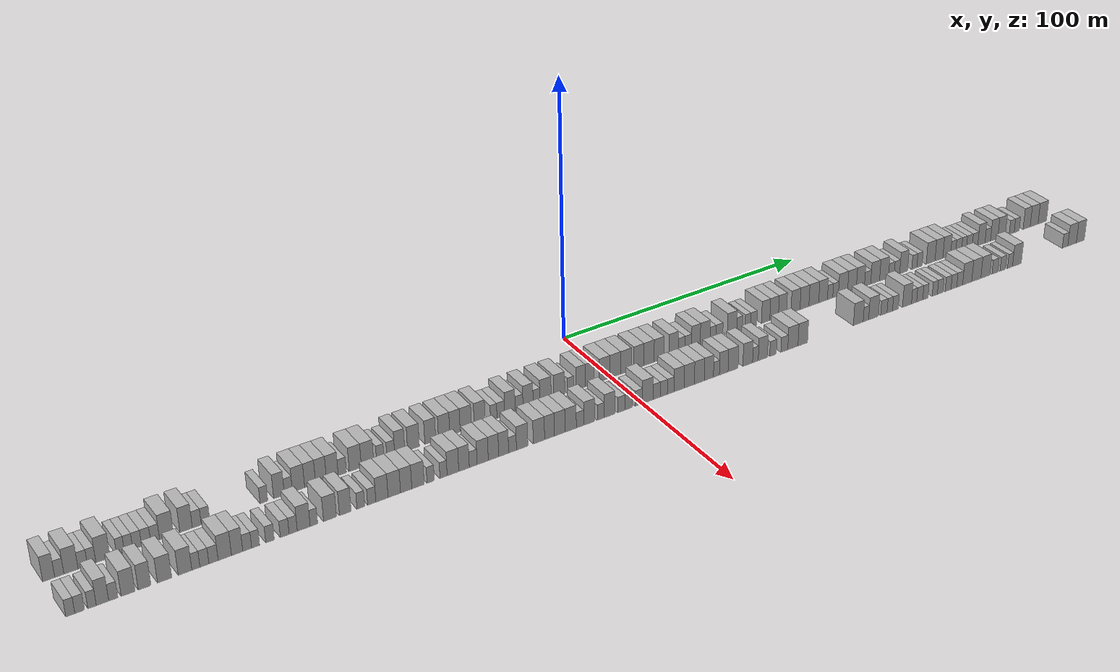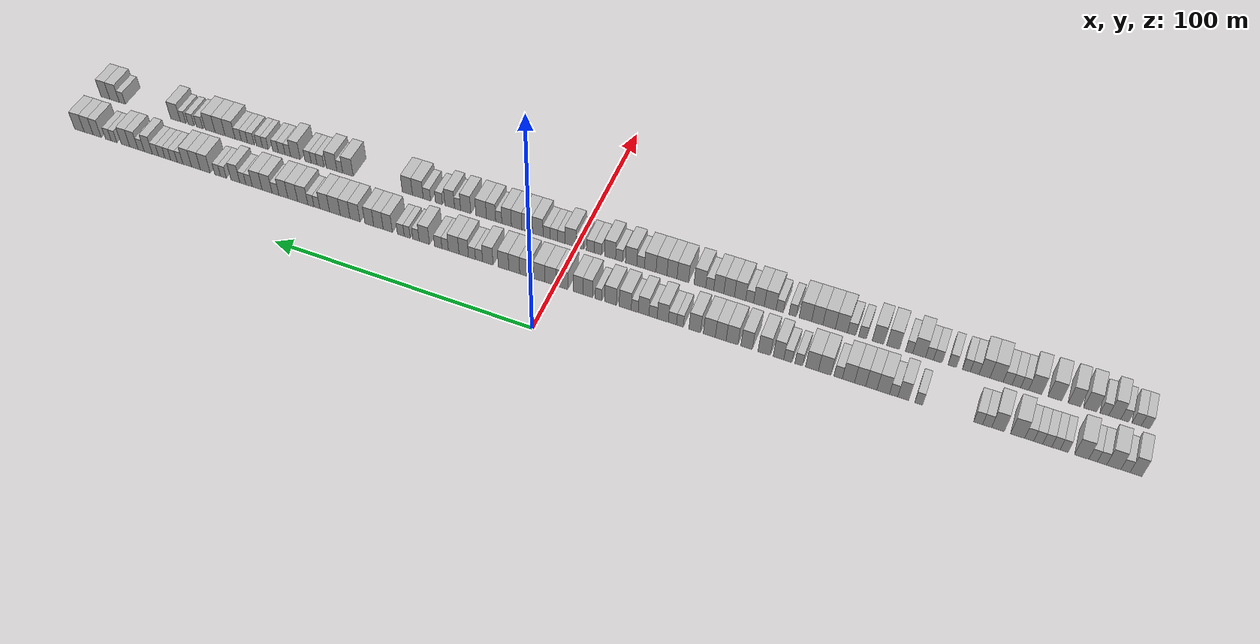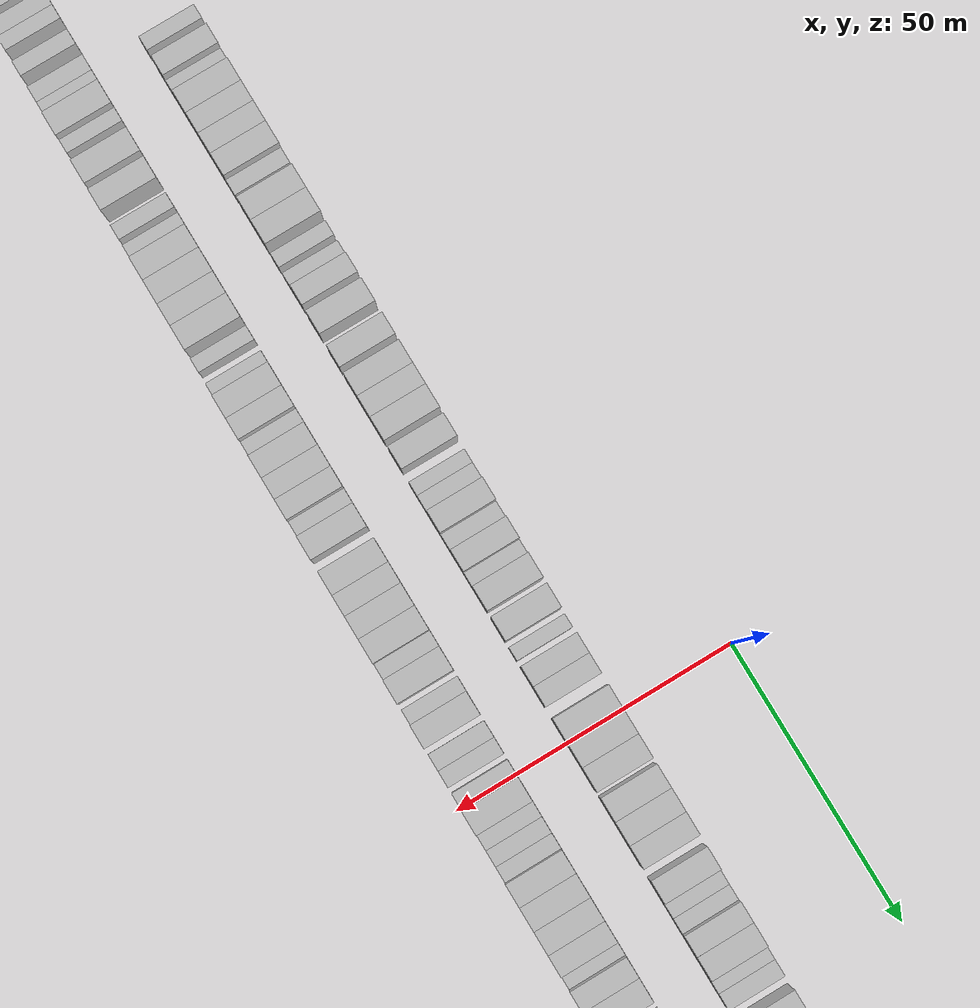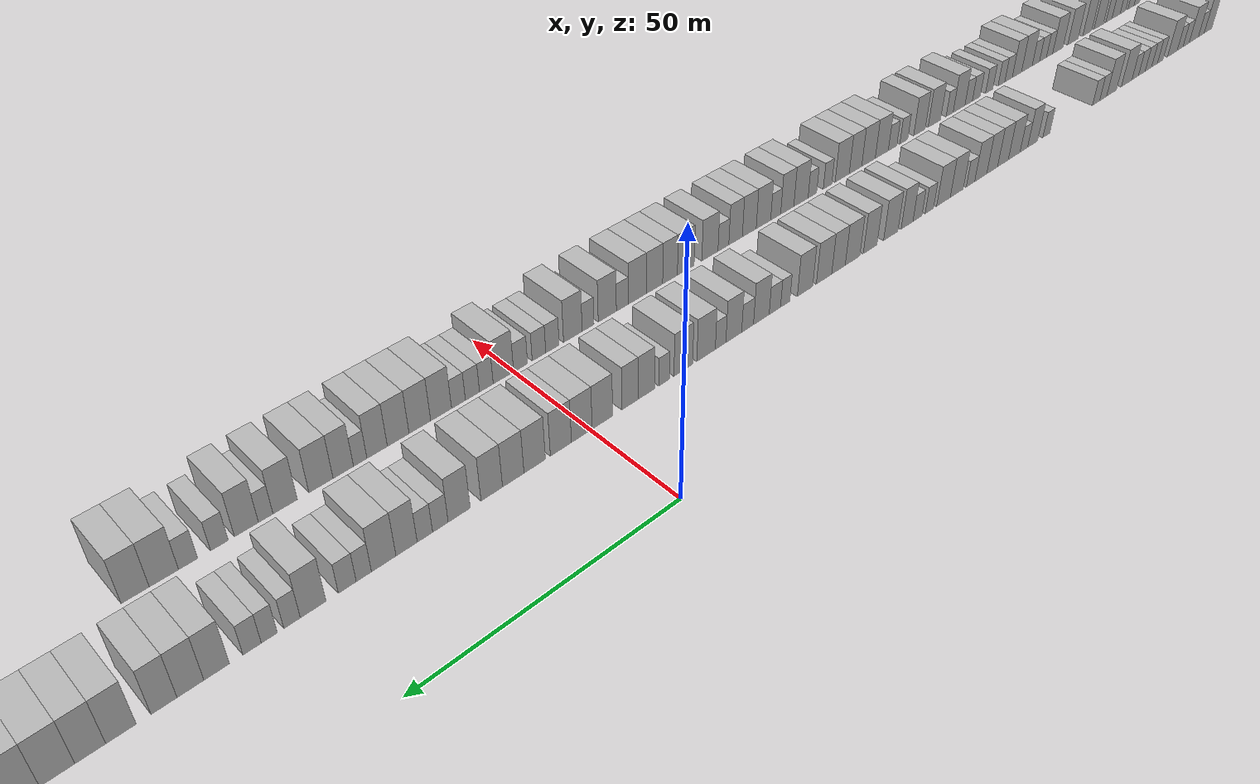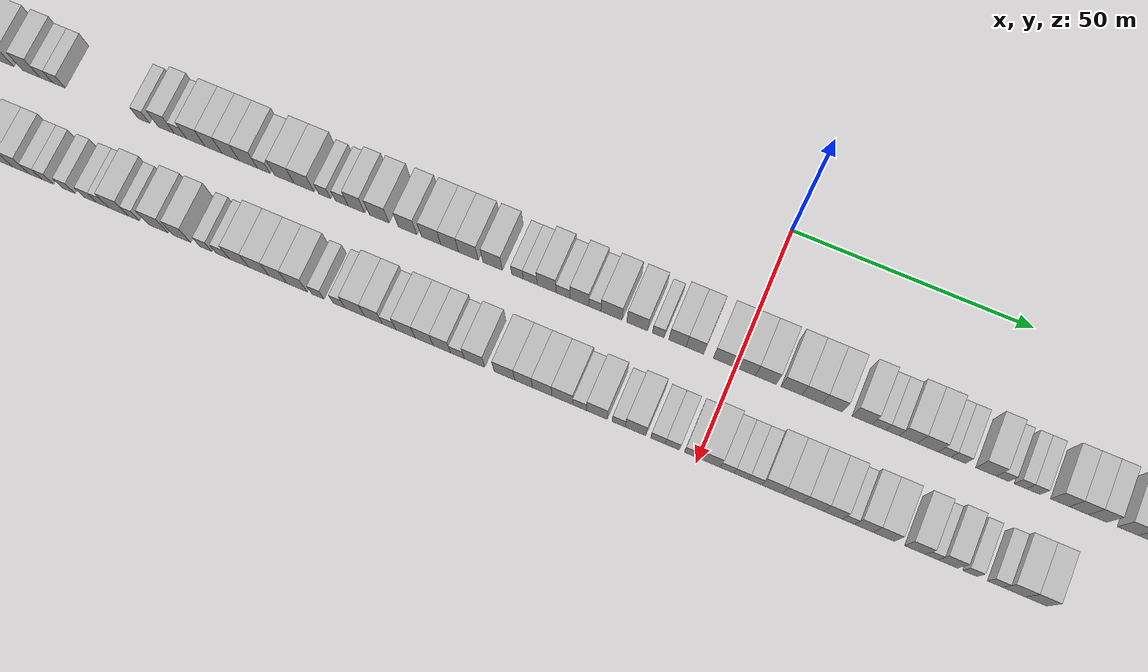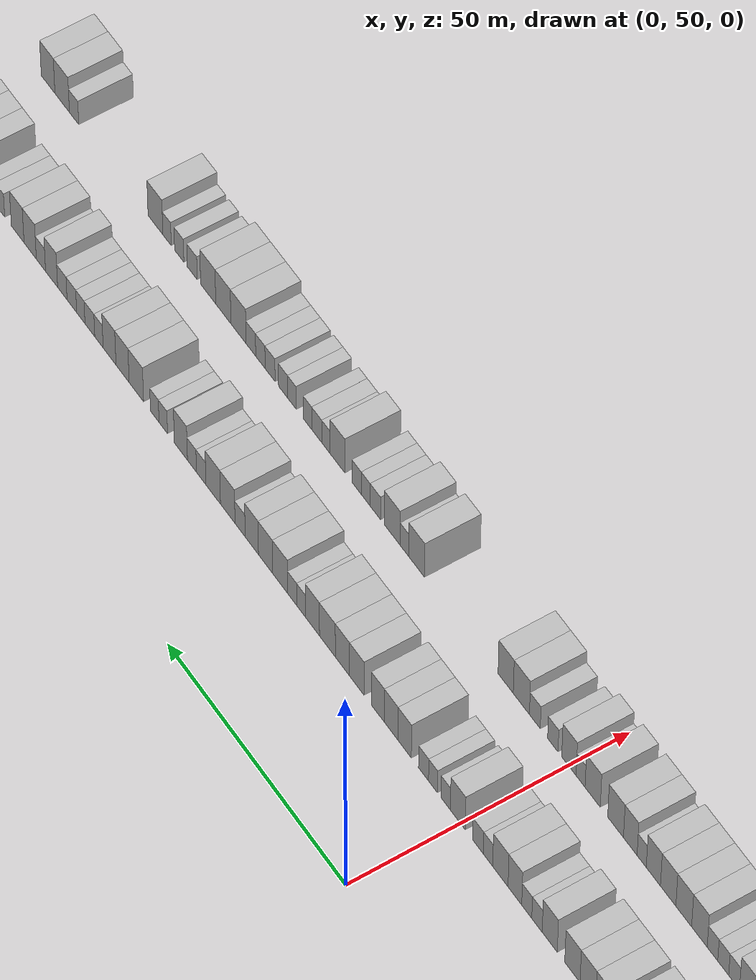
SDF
<sdf version="1.6">
 <world name="default">
  <scene>
   <sky><clouds><speed>12</speed></clouds></sky>
   <ambient>0.4 0.4 0.4 1</ambient>
   <background>0.7 0.7 0.7 1</background>
   <shadows>1</shadows>
  </scene>
  <gravity>0 0 -9.8066</gravity>
  <magnetic_field>6e-06 2.3e-05 -4.2e-05</magnetic_field>
  <physics default="0" name="default_physics" type="ode">
   <ode>
    <solver>
     <type>quick</type>
     <iters>10</iters>
     <sor>1.0</sor>
     <use_dynamic_moi_rescaling>0</use_dynamic_moi_rescaling>
    </solver>
    <constraints>
     <cfm>0</cfm>
     <erp>0.2</erp>
     <contact_max_correcting_vel>100</contact_max_correcting_vel>
     <contact_surface_layer>0.001</contact_surface_layer>
    </constraints>
   </ode>
   <max_step_size>0.004</max_step_size>
   <real_time_factor>1</real_time_factor>
   <real_time_update_rate>250</real_time_update_rate>
  </physics>
  <light name="sun" type="directional">
   <pose>0 0 10 0 0 0</pose>
   <diffuse>0.8 0.8 0.8 1</diffuse>
   <specular>0.2 0.2 0.2 1</specular>
   <attenuation>
    <range>1000</range>
    <constant>0.9</constant>
    <linear>0.01</linear>
    <quadratic>0.001</quadratic>
   </attenuation>
   <direction>-0.5 0.1 -0.9</direction>
  </light>
  <model name="building_1">
   <static>1</static>
   <pose>25.0000 -196.1872 0 0.000000 0.000000 0.000000</pose>
   <link name="link">
    <pose>0 0 4.50 0 0 0</pose>
    <collision name="collision"><geometry><box><size>10.0000 3.6256 9.0000</size></box></geometry></collision>
    <visual name="visual">
     <cast_shadows>0</cast_shadows>
     <geometry><box><size>10.0000 3.6256 9.0000</size></box></geometry>
     <material>
      <script>
       <uri>model://HANNAS_wall/materials/scripts</uri>
       <uri>model://HANNAS_wall/materials/textures</uri>
       <name>vrc/HANNAS_wall</name>
      </script>
     </material>
    </visual>
   </link>
  </model>
  <model name="building_2">
   <static>1</static>
   <pose>25.0000 -192.9768 0 0.000000 0.000000 0.000000</pose>
   <link name="link">
    <pose>0 0 3.00 0 0 0</pose>
    <collision name="collision"><geometry><box><size>10.0000 2.7953 6.0000</size></box></geometry></collision>
    <visual name="visual">
     <cast_shadows>0</cast_shadows>
     <geometry><box><size>10.0000 2.7953 6.0000</size></box></geometry>
     <material>
      <script>
       <uri>model://HANNAS_wall/materials/scripts</uri>
       <uri>model://HANNAS_wall/materials/textures</uri>
       <name>vrc/HANNAS_wall</name>
      </script>
     </material>
    </visual>
   </link>
  </model>
  <model name="building_3">
   <static>1</static>
   <pose>25.0000 -189.4172 0 0.000000 0.000000 0.000000</pose>
   <link name="link">
    <pose>0 0 4.50 0 0 0</pose>
    <collision name="collision"><geometry><box><size>10.0000 4.3239 9.0000</size></box></geometry></collision>
    <visual name="visual">
     <cast_shadows>0</cast_shadows>
     <geometry><box><size>10.0000 4.3239 9.0000</size></box></geometry>
     <material>
      <script>
       <uri>model://HANNAS_wall/materials/scripts</uri>
       <uri>model://HANNAS_wall/materials/textures</uri>
       <name>vrc/HANNAS_wall</name>
      </script>
     </material>
    </visual>
   </link>
  </model>
  <model name="building_4">
   <static>1</static>
   <pose>25.0000 -185.8251 0 0.000000 0.000000 0.000000</pose>
   <link name="link">
    <pose>0 0 3.00 0 0 0</pose>
    <collision name="collision"><geometry><box><size>10.0000 2.8601 6.0000</size></box></geometry></collision>
    <visual name="visual">
     <cast_shadows>0</cast_shadows>
     <geometry><box><size>10.0000 2.8601 6.0000</size></box></geometry>
     <material>
      <script>
       <uri>model://HANNAS_wall/materials/scripts</uri>
       <uri>model://HANNAS_wall/materials/textures</uri>
       <name>vrc/HANNAS_wall</name>
      </script>
     </material>
    </visual>
   </link>
  </model>
  <model name="building_5">
   <static>1</static>
   <pose>25.0000 -183.0920 0 0.000000 0.000000 0.000000</pose>
   <link name="link">
    <pose>0 0 3.00 0 0 0</pose>
    <collision name="collision"><geometry><box><size>10.0000 2.6062 6.0000</size></box></geometry></collision>
    <visual name="visual">
     <cast_shadows>0</cast_shadows>
     <geometry><box><size>10.0000 2.6062 6.0000</size></box></geometry>
     <material>
      <script>
       <uri>model://HANNAS_wall/materials/scripts</uri>
       <uri>model://HANNAS_wall/materials/textures</uri>
       <name>vrc/HANNAS_wall</name>
      </script>
     </material>
    </visual>
   </link>
  </model>
  <model name="building_6">
   <static>1</static>
   <pose>25.0000 -179.5854 0 0.000000 0.000000 0.000000</pose>
   <link name="link">
    <pose>0 0 4.50 0 0 0</pose>
    <collision name="collision"><geometry><box><size>10.0000 4.4069 9.0000</size></box></geometry></collision>
    <visual name="visual">
     <cast_shadows>0</cast_shadows>
     <geometry><box><size>10.0000 4.4069 9.0000</size></box></geometry>
     <material>
      <script>
       <uri>model://HANNAS_wall/materials/scripts</uri>
       <uri>model://HANNAS_wall/materials/textures</uri>
       <name>vrc/HANNAS_wall</name>
      </script>
     </material>
    </visual>
   </link>
  </model>
  <model name="building_7">
   <static>1</static>
   <pose>25.0000 -174.1378 0 0.000000 0.000000 0.000000</pose>
   <link name="link">
    <pose>0 0 3.00 0 0 0</pose>
    <collision name="collision"><geometry><box><size>10.0000 2.4883 6.0000</size></box></geometry></collision>
    <visual name="visual">
     <cast_shadows>0</cast_shadows>
     <geometry><box><size>10.0000 2.4883 6.0000</size></box></geometry>
     <material>
      <script>
       <uri>model://HANNAS_wall/materials/scripts</uri>
       <uri>model://HANNAS_wall/materials/textures</uri>
       <name>vrc/HANNAS_wall</name>
      </script>
     </material>
    </visual>
   </link>
  </model>
  <model name="building_8">
   <static>1</static>
   <pose>25.0000 -171.6017 0 0.000000 0.000000 0.000000</pose>
   <link name="link">
    <pose>0 0 3.00 0 0 0</pose>
    <collision name="collision"><geometry><box><size>10.0000 2.5839 6.0000</size></box></geometry></collision>
    <visual name="visual">
     <cast_shadows>0</cast_shadows>
     <geometry><box><size>10.0000 2.5839 6.0000</size></box></geometry>
     <material>
      <script>
       <uri>model://HANNAS_wall/materials/scripts</uri>
       <uri>model://HANNAS_wall/materials/textures</uri>
       <name>vrc/HANNAS_wall</name>
      </script>
     </material>
    </visual>
   </link>
  </model>
  <model name="building_9">
   <static>1</static>
   <pose>25.0000 -168.9097 0 0.000000 0.000000 0.000000</pose>
   <link name="link">
    <pose>0 0 3.00 0 0 0</pose>
    <collision name="collision"><geometry><box><size>10.0000 2.8001 6.0000</size></box></geometry></collision>
    <visual name="visual">
     <cast_shadows>0</cast_shadows>
     <geometry><box><size>10.0000 2.8001 6.0000</size></box></geometry>
     <material>
      <script>
       <uri>model://HANNAS_wall/materials/scripts</uri>
       <uri>model://HANNAS_wall/materials/textures</uri>
       <name>vrc/HANNAS_wall</name>
      </script>
     </material>
    </visual>
   </link>
  </model>
  <model name="building_10">
   <static>1</static>
   <pose>25.0000 -166.0650 0 0.000000 0.000000 0.000000</pose>
   <link name="link">
    <pose>0 0 3.00 0 0 0</pose>
    <collision name="collision"><geometry><box><size>10.0000 2.8893 6.0000</size></box></geometry></collision>
    <visual name="visual">
     <cast_shadows>0</cast_shadows>
     <geometry><box><size>10.0000 2.8893 6.0000</size></box></geometry>
     <material>
      <script>
       <uri>model://HANNAS_wall/materials/scripts</uri>
       <uri>model://HANNAS_wall/materials/textures</uri>
       <name>vrc/HANNAS_wall</name>
      </script>
     </material>
    </visual>
   </link>
  </model>
  <model name="building_11">
   <static>1</static>
   <pose>25.0000 -163.2217 0 0.000000 0.000000 0.000000</pose>
   <link name="link">
    <pose>0 0 3.00 0 0 0</pose>
    <collision name="collision"><geometry><box><size>10.0000 2.7973 6.0000</size></box></geometry></collision>
    <visual name="visual">
     <cast_shadows>0</cast_shadows>
     <geometry><box><size>10.0000 2.7973 6.0000</size></box></geometry>
     <material>
      <script>
       <uri>model://HANNAS_wall/materials/scripts</uri>
       <uri>model://HANNAS_wall/materials/textures</uri>
       <name>vrc/HANNAS_wall</name>
      </script>
     </material>
    </visual>
   </link>
  </model>
  <model name="building_12">
   <static>1</static>
   <pose>25.0000 -159.5874 0 0.000000 0.000000 0.000000</pose>
   <link name="link">
    <pose>0 0 4.50 0 0 0</pose>
    <collision name="collision"><geometry><box><size>10.0000 4.4713 9.0000</size></box></geometry></collision>
    <visual name="visual">
     <cast_shadows>0</cast_shadows>
     <geometry><box><size>10.0000 4.4713 9.0000</size></box></geometry>
     <material>
      <script>
       <uri>model://HANNAS_wall/materials/scripts</uri>
       <uri>model://HANNAS_wall/materials/textures</uri>
       <name>vrc/HANNAS_wall</name>
      </script>
     </material>
    </visual>
   </link>
  </model>
  <model name="building_13">
   <static>1</static>
   <pose>25.0000 -153.3318 0 0.000000 0.000000 0.000000</pose>
   <link name="link">
    <pose>0 0 4.50 0 0 0</pose>
    <collision name="collision"><geometry><box><size>10.0000 4.0397 9.0000</size></box></geometry></collision>
    <visual name="visual">
     <cast_shadows>0</cast_shadows>
     <geometry><box><size>10.0000 4.0397 9.0000</size></box></geometry>
     <material>
      <script>
       <uri>model://HANNAS_wall/materials/scripts</uri>
       <uri>model://HANNAS_wall/materials/textures</uri>
       <name>vrc/HANNAS_wall</name>
      </script>
     </material>
    </visual>
   </link>
  </model>
  <model name="building_14">
   <static>1</static>
   <pose>25.0000 -149.8733 0 0.000000 0.000000 0.000000</pose>
   <link name="link">
    <pose>0 0 3.00 0 0 0</pose>
    <collision name="collision"><geometry><box><size>10.0000 2.8774 6.0000</size></box></geometry></collision>
    <visual name="visual">
     <cast_shadows>0</cast_shadows>
     <geometry><box><size>10.0000 2.8774 6.0000</size></box></geometry>
     <material>
      <script>
       <uri>model://HANNAS_wall/materials/scripts</uri>
       <uri>model://HANNAS_wall/materials/textures</uri>
       <name>vrc/HANNAS_wall</name>
      </script>
     </material>
    </visual>
   </link>
  </model>
  <model name="building_15">
   <static>1</static>
   <pose>25.0000 -147.0104 0 0.000000 0.000000 0.000000</pose>
   <link name="link">
    <pose>0 0 3.00 0 0 0</pose>
    <collision name="collision"><geometry><box><size>10.0000 2.8483 6.0000</size></box></geometry></collision>
    <visual name="visual">
     <cast_shadows>0</cast_shadows>
     <geometry><box><size>10.0000 2.8483 6.0000</size></box></geometry>
     <material>
      <script>
       <uri>model://HANNAS_wall/materials/scripts</uri>
       <uri>model://HANNAS_wall/materials/textures</uri>
       <name>vrc/HANNAS_wall</name>
      </script>
     </material>
    </visual>
   </link>
  </model>
  <model name="building_16">
   <static>1</static>
   <pose>25.0000 -127.7283 0 0.000000 0.000000 0.000000</pose>
   <link name="link">
    <pose>0 0 3.00 0 0 0</pose>
    <collision name="collision"><geometry><box><size>10.0000 2.5720 6.0000</size></box></geometry></collision>
    <visual name="visual">
     <cast_shadows>0</cast_shadows>
     <geometry><box><size>10.0000 2.5720 6.0000</size></box></geometry>
     <material>
      <script>
       <uri>model://HANNAS_wall/materials/scripts</uri>
       <uri>model://HANNAS_wall/materials/textures</uri>
       <name>vrc/HANNAS_wall</name>
      </script>
     </material>
    </visual>
   </link>
  </model>
  <model name="building_17">
   <static>1</static>
   <pose>25.0000 -122.6291 0 0.000000 0.000000 0.000000</pose>
   <link name="link">
    <pose>0 0 4.50 0 0 0</pose>
    <collision name="collision"><geometry><box><size>10.0000 3.6263 9.0000</size></box></geometry></collision>
    <visual name="visual">
     <cast_shadows>0</cast_shadows>
     <geometry><box><size>10.0000 3.6263 9.0000</size></box></geometry>
     <material>
      <script>
       <uri>model://HANNAS_wall/materials/scripts</uri>
       <uri>model://HANNAS_wall/materials/textures</uri>
       <name>vrc/HANNAS_wall</name>
      </script>
     </material>
    </visual>
   </link>
  </model>
  <model name="building_18">
   <static>1</static>
   <pose>25.0000 -119.4527 0 0.000000 0.000000 0.000000</pose>
   <link name="link">
    <pose>0 0 3.00 0 0 0</pose>
    <collision name="collision"><geometry><box><size>10.0000 2.7266 6.0000</size></box></geometry></collision>
    <visual name="visual">
     <cast_shadows>0</cast_shadows>
     <geometry><box><size>10.0000 2.7266 6.0000</size></box></geometry>
     <material>
      <script>
       <uri>model://HANNAS_wall/materials/scripts</uri>
       <uri>model://HANNAS_wall/materials/textures</uri>
       <name>vrc/HANNAS_wall</name>
      </script>
     </material>
    </visual>
   </link>
  </model>
  <model name="building_19">
   <static>1</static>
   <pose>25.0000 -115.9980 0 0.000000 0.000000 0.000000</pose>
   <link name="link">
    <pose>0 0 4.50 0 0 0</pose>
    <collision name="collision"><geometry><box><size>10.0000 4.1827 9.0000</size></box></geometry></collision>
    <visual name="visual">
     <cast_shadows>0</cast_shadows>
     <geometry><box><size>10.0000 4.1827 9.0000</size></box></geometry>
     <material>
      <script>
       <uri>model://HANNAS_wall/materials/scripts</uri>
       <uri>model://HANNAS_wall/materials/textures</uri>
       <name>vrc/HANNAS_wall</name>
      </script>
     </material>
    </visual>
   </link>
  </model>
  <model name="building_20">
   <static>1</static>
   <pose>25.0000 -112.0309 0 0.000000 0.000000 0.000000</pose>
   <link name="link">
    <pose>0 0 4.50 0 0 0</pose>
    <collision name="collision"><geometry><box><size>10.0000 3.7516 9.0000</size></box></geometry></collision>
    <visual name="visual">
     <cast_shadows>0</cast_shadows>
     <geometry><box><size>10.0000 3.7516 9.0000</size></box></geometry>
     <material>
      <script>
       <uri>model://HANNAS_wall/materials/scripts</uri>
       <uri>model://HANNAS_wall/materials/textures</uri>
       <name>vrc/HANNAS_wall</name>
      </script>
     </material>
    </visual>
   </link>
  </model>
  <model name="building_21">
   <static>1</static>
   <pose>25.0000 -108.2839 0 0.000000 0.000000 0.000000</pose>
   <link name="link">
    <pose>0 0 4.50 0 0 0</pose>
    <collision name="collision"><geometry><box><size>10.0000 3.7425 9.0000</size></box></geometry></collision>
    <visual name="visual">
     <cast_shadows>0</cast_shadows>
     <geometry><box><size>10.0000 3.7425 9.0000</size></box></geometry>
     <material>
      <script>
       <uri>model://HANNAS_wall/materials/scripts</uri>
       <uri>model://HANNAS_wall/materials/textures</uri>
       <name>vrc/HANNAS_wall</name>
      </script>
     </material>
    </visual>
   </link>
  </model>
  <model name="building_22">
   <static>1</static>
   <pose>25.0000 -104.3630 0 0.000000 0.000000 0.000000</pose>
   <link name="link">
    <pose>0 0 4.50 0 0 0</pose>
    <collision name="collision"><geometry><box><size>10.0000 4.0994 9.0000</size></box></geometry></collision>
    <visual name="visual">
     <cast_shadows>0</cast_shadows>
     <geometry><box><size>10.0000 4.0994 9.0000</size></box></geometry>
     <material>
      <script>
       <uri>model://HANNAS_wall/materials/scripts</uri>
       <uri>model://HANNAS_wall/materials/textures</uri>
       <name>vrc/HANNAS_wall</name>
      </script>
     </material>
    </visual>
   </link>
  </model>
  <model name="building_23">
   <static>1</static>
   <pose>25.0000 -100.8907 0 0.000000 0.000000 0.000000</pose>
   <link name="link">
    <pose>0 0 3.00 0 0 0</pose>
    <collision name="collision"><geometry><box><size>10.0000 2.8451 6.0000</size></box></geometry></collision>
    <visual name="visual">
     <cast_shadows>0</cast_shadows>
     <geometry><box><size>10.0000 2.8451 6.0000</size></box></geometry>
     <material>
      <script>
       <uri>model://HANNAS_wall/materials/scripts</uri>
       <uri>model://HANNAS_wall/materials/textures</uri>
       <name>vrc/HANNAS_wall</name>
      </script>
     </material>
    </visual>
   </link>
  </model>
  <model name="building_24">
   <static>1</static>
   <pose>25.0000 -96.3340 0 0.000000 0.000000 0.000000</pose>
   <link name="link">
    <pose>0 0 4.50 0 0 0</pose>
    <collision name="collision"><geometry><box><size>10.0000 4.2683 9.0000</size></box></geometry></collision>
    <visual name="visual">
     <cast_shadows>0</cast_shadows>
     <geometry><box><size>10.0000 4.2683 9.0000</size></box></geometry>
     <material>
      <script>
       <uri>model://HANNAS_wall/materials/scripts</uri>
       <uri>model://HANNAS_wall/materials/textures</uri>
       <name>vrc/HANNAS_wall</name>
      </script>
     </material>
    </visual>
   </link>
  </model>
  <model name="building_25">
   <static>1</static>
   <pose>25.0000 -92.0035 0 0.000000 0.000000 0.000000</pose>
   <link name="link">
    <pose>0 0 4.50 0 0 0</pose>
    <collision name="collision"><geometry><box><size>10.0000 4.3929 9.0000</size></box></geometry></collision>
    <visual name="visual">
     <cast_shadows>0</cast_shadows>
     <geometry><box><size>10.0000 4.3929 9.0000</size></box></geometry>
     <material>
      <script>
       <uri>model://HANNAS_wall/materials/scripts</uri>
       <uri>model://HANNAS_wall/materials/textures</uri>
       <name>vrc/HANNAS_wall</name>
      </script>
     </material>
    </visual>
   </link>
  </model>
  <model name="building_26">
   <static>1</static>
   <pose>25.0000 -87.4747 0 0.000000 0.000000 0.000000</pose>
   <link name="link">
    <pose>0 0 3.00 0 0 0</pose>
    <collision name="collision"><geometry><box><size>10.0000 2.6648 6.0000</size></box></geometry></collision>
    <visual name="visual">
     <cast_shadows>0</cast_shadows>
     <geometry><box><size>10.0000 2.6648 6.0000</size></box></geometry>
     <material>
      <script>
       <uri>model://HANNAS_wall/materials/scripts</uri>
       <uri>model://HANNAS_wall/materials/textures</uri>
       <name>vrc/HANNAS_wall</name>
      </script>
     </material>
    </visual>
   </link>
  </model>
  <model name="building_27">
   <static>1</static>
   <pose>25.0000 -83.7285 0 0.000000 0.000000 0.000000</pose>
   <link name="link">
    <pose>0 0 3.00 0 0 0</pose>
    <collision name="collision"><geometry><box><size>10.0000 2.8275 6.0000</size></box></geometry></collision>
    <visual name="visual">
     <cast_shadows>0</cast_shadows>
     <geometry><box><size>10.0000 2.8275 6.0000</size></box></geometry>
     <material>
      <script>
       <uri>model://HANNAS_wall/materials/scripts</uri>
       <uri>model://HANNAS_wall/materials/textures</uri>
       <name>vrc/HANNAS_wall</name>
      </script>
     </material>
    </visual>
   </link>
  </model>
  <model name="building_28">
   <static>1</static>
   <pose>25.0000 -80.5029 0 0.000000 0.000000 0.000000</pose>
   <link name="link">
    <pose>0 0 4.50 0 0 0</pose>
    <collision name="collision"><geometry><box><size>10.0000 3.6236 9.0000</size></box></geometry></collision>
    <visual name="visual">
     <cast_shadows>0</cast_shadows>
     <geometry><box><size>10.0000 3.6236 9.0000</size></box></geometry>
     <material>
      <script>
       <uri>model://HANNAS_wall/materials/scripts</uri>
       <uri>model://HANNAS_wall/materials/textures</uri>
       <name>vrc/HANNAS_wall</name>
      </script>
     </material>
    </visual>
   </link>
  </model>
  <model name="building_29">
   <static>1</static>
   <pose>25.0000 -75.5467 0 0.000000 0.000000 0.000000</pose>
   <link name="link">
    <pose>0 0 4.50 0 0 0</pose>
    <collision name="collision"><geometry><box><size>10.0000 4.2889 9.0000</size></box></geometry></collision>
    <visual name="visual">
     <cast_shadows>0</cast_shadows>
     <geometry><box><size>10.0000 4.2889 9.0000</size></box></geometry>
     <material>
      <script>
       <uri>model://HANNAS_wall/materials/scripts</uri>
       <uri>model://HANNAS_wall/materials/textures</uri>
       <name>vrc/HANNAS_wall</name>
      </script>
     </material>
    </visual>
   </link>
  </model>
  <model name="building_30">
   <static>1</static>
   <pose>25.0000 -69.4031 0 0.000000 0.000000 0.000000</pose>
   <link name="link">
    <pose>0 0 4.50 0 0 0</pose>
    <collision name="collision"><geometry><box><size>10.0000 3.9982 9.0000</size></box></geometry></collision>
    <visual name="visual">
     <cast_shadows>0</cast_shadows>
     <geometry><box><size>10.0000 3.9982 9.0000</size></box></geometry>
     <material>
      <script>
       <uri>model://HANNAS_wall/materials/scripts</uri>
       <uri>model://HANNAS_wall/materials/textures</uri>
       <name>vrc/HANNAS_wall</name>
      </script>
     </material>
    </visual>
   </link>
  </model>
  <model name="building_31">
   <static>1</static>
   <pose>25.0000 -64.3107 0 0.000000 0.000000 0.000000</pose>
   <link name="link">
    <pose>0 0 4.50 0 0 0</pose>
    <collision name="collision"><geometry><box><size>10.0000 4.1865 9.0000</size></box></geometry></collision>
    <visual name="visual">
     <cast_shadows>0</cast_shadows>
     <geometry><box><size>10.0000 4.1865 9.0000</size></box></geometry>
     <material>
      <script>
       <uri>model://HANNAS_wall/materials/scripts</uri>
       <uri>model://HANNAS_wall/materials/textures</uri>
       <name>vrc/HANNAS_wall</name>
      </script>
     </material>
    </visual>
   </link>
  </model>
  <model name="building_32">
   <static>1</static>
   <pose>25.0000 -60.3107 0 0.000000 0.000000 0.000000</pose>
   <link name="link">
    <pose>0 0 4.50 0 0 0</pose>
    <collision name="collision"><geometry><box><size>10.0000 3.8135 9.0000</size></box></geometry></collision>
    <visual name="visual">
     <cast_shadows>0</cast_shadows>
     <geometry><box><size>10.0000 3.8135 9.0000</size></box></geometry>
     <material>
      <script>
       <uri>model://HANNAS_wall/materials/scripts</uri>
       <uri>model://HANNAS_wall/materials/textures</uri>
       <name>vrc/HANNAS_wall</name>
      </script>
     </material>
    </visual>
   </link>
  </model>
  <model name="building_33">
   <static>1</static>
   <pose>25.0000 -56.2787 0 0.000000 0.000000 0.000000</pose>
   <link name="link">
    <pose>0 0 4.50 0 0 0</pose>
    <collision name="collision"><geometry><box><size>10.0000 4.2505 9.0000</size></box></geometry></collision>
    <visual name="visual">
     <cast_shadows>0</cast_shadows>
     <geometry><box><size>10.0000 4.2505 9.0000</size></box></geometry>
     <material>
      <script>
       <uri>model://HANNAS_wall/materials/scripts</uri>
       <uri>model://HANNAS_wall/materials/textures</uri>
       <name>vrc/HANNAS_wall</name>
      </script>
     </material>
    </visual>
   </link>
  </model>
  <model name="building_34">
   <static>1</static>
   <pose>25.0000 -51.0854 0 0.000000 0.000000 0.000000</pose>
   <link name="link">
    <pose>0 0 4.50 0 0 0</pose>
    <collision name="collision"><geometry><box><size>10.0000 4.1361 9.0000</size></box></geometry></collision>
    <visual name="visual">
     <cast_shadows>0</cast_shadows>
     <geometry><box><size>10.0000 4.1361 9.0000</size></box></geometry>
     <material>
      <script>
       <uri>model://HANNAS_wall/materials/scripts</uri>
       <uri>model://HANNAS_wall/materials/textures</uri>
       <name>vrc/HANNAS_wall</name>
      </script>
     </material>
    </visual>
   </link>
  </model>
  <model name="building_35">
   <static>1</static>
   <pose>25.0000 -45.7949 0 0.000000 0.000000 0.000000</pose>
   <link name="link">
    <pose>0 0 3.00 0 0 0</pose>
    <collision name="collision"><geometry><box><size>10.0000 2.4448 6.0000</size></box></geometry></collision>
    <visual name="visual">
     <cast_shadows>0</cast_shadows>
     <geometry><box><size>10.0000 2.4448 6.0000</size></box></geometry>
     <material>
      <script>
       <uri>model://HANNAS_wall/materials/scripts</uri>
       <uri>model://HANNAS_wall/materials/textures</uri>
       <name>vrc/HANNAS_wall</name>
      </script>
     </material>
    </visual>
   </link>
  </model>
  <model name="building_36">
   <static>1</static>
   <pose>25.0000 -43.0886 0 0.000000 0.000000 0.000000</pose>
   <link name="link">
    <pose>0 0 3.00 0 0 0</pose>
    <collision name="collision"><geometry><box><size>10.0000 2.9679 6.0000</size></box></geometry></collision>
    <visual name="visual">
     <cast_shadows>0</cast_shadows>
     <geometry><box><size>10.0000 2.9679 6.0000</size></box></geometry>
     <material>
      <script>
       <uri>model://HANNAS_wall/materials/scripts</uri>
       <uri>model://HANNAS_wall/materials/textures</uri>
       <name>vrc/HANNAS_wall</name>
      </script>
     </material>
    </visual>
   </link>
  </model>
  <model name="building_37">
   <static>1</static>
   <pose>25.0000 -39.5950 0 0.000000 0.000000 0.000000</pose>
   <link name="link">
    <pose>0 0 4.50 0 0 0</pose>
    <collision name="collision"><geometry><box><size>10.0000 4.0194 9.0000</size></box></geometry></collision>
    <visual name="visual">
     <cast_shadows>0</cast_shadows>
     <geometry><box><size>10.0000 4.0194 9.0000</size></box></geometry>
     <material>
      <script>
       <uri>model://HANNAS_wall/materials/scripts</uri>
       <uri>model://HANNAS_wall/materials/textures</uri>
       <name>vrc/HANNAS_wall</name>
      </script>
     </material>
    </visual>
   </link>
  </model>
  <model name="building_38">
   <static>1</static>
   <pose>25.0000 -36.0967 0 0.000000 0.000000 0.000000</pose>
   <link name="link">
    <pose>0 0 3.00 0 0 0</pose>
    <collision name="collision"><geometry><box><size>10.0000 2.9772 6.0000</size></box></geometry></collision>
    <visual name="visual">
     <cast_shadows>0</cast_shadows>
     <geometry><box><size>10.0000 2.9772 6.0000</size></box></geometry>
     <material>
      <script>
       <uri>model://HANNAS_wall/materials/scripts</uri>
       <uri>model://HANNAS_wall/materials/textures</uri>
       <name>vrc/HANNAS_wall</name>
      </script>
     </material>
    </visual>
   </link>
  </model>
  <model name="building_39">
   <static>1</static>
   <pose>25.0000 -32.6486 0 0.000000 0.000000 0.000000</pose>
   <link name="link">
    <pose>0 0 4.50 0 0 0</pose>
    <collision name="collision"><geometry><box><size>10.0000 3.9190 9.0000</size></box></geometry></collision>
    <visual name="visual">
     <cast_shadows>0</cast_shadows>
     <geometry><box><size>10.0000 3.9190 9.0000</size></box></geometry>
     <material>
      <script>
       <uri>model://HANNAS_wall/materials/scripts</uri>
       <uri>model://HANNAS_wall/materials/textures</uri>
       <name>vrc/HANNAS_wall</name>
      </script>
     </material>
    </visual>
   </link>
  </model>
  <model name="building_40">
   <static>1</static>
   <pose>25.0000 -29.4030 0 0.000000 0.000000 0.000000</pose>
   <link name="link">
    <pose>0 0 3.00 0 0 0</pose>
    <collision name="collision"><geometry><box><size>10.0000 2.5723 6.0000</size></box></geometry></collision>
    <visual name="visual">
     <cast_shadows>0</cast_shadows>
     <geometry><box><size>10.0000 2.5723 6.0000</size></box></geometry>
     <material>
      <script>
       <uri>model://HANNAS_wall/materials/scripts</uri>
       <uri>model://HANNAS_wall/materials/textures</uri>
       <name>vrc/HANNAS_wall</name>
      </script>
     </material>
    </visual>
   </link>
  </model>
  <model name="building_41">
   <static>1</static>
   <pose>25.0000 -25.9004 0 0.000000 0.000000 0.000000</pose>
   <link name="link">
    <pose>0 0 4.50 0 0 0</pose>
    <collision name="collision"><geometry><box><size>10.0000 4.4328 9.0000</size></box></geometry></collision>
    <visual name="visual">
     <cast_shadows>0</cast_shadows>
     <geometry><box><size>10.0000 4.4328 9.0000</size></box></geometry>
     <material>
      <script>
       <uri>model://HANNAS_wall/materials/scripts</uri>
       <uri>model://HANNAS_wall/materials/textures</uri>
       <name>vrc/HANNAS_wall</name>
      </script>
     </material>
    </visual>
   </link>
  </model>
  <model name="building_42">
   <static>1</static>
   <pose>25.0000 -20.5050 0 0.000000 0.000000 0.000000</pose>
   <link name="link">
    <pose>0 0 4.50 0 0 0</pose>
    <collision name="collision"><geometry><box><size>10.0000 4.3582 9.0000</size></box></geometry></collision>
    <visual name="visual">
     <cast_shadows>0</cast_shadows>
     <geometry><box><size>10.0000 4.3582 9.0000</size></box></geometry>
     <material>
      <script>
       <uri>model://HANNAS_wall/materials/scripts</uri>
       <uri>model://HANNAS_wall/materials/textures</uri>
       <name>vrc/HANNAS_wall</name>
      </script>
     </material>
    </visual>
   </link>
  </model>
  <model name="building_43">
   <static>1</static>
   <pose>25.0000 -16.1089 0 0.000000 0.000000 0.000000</pose>
   <link name="link">
    <pose>0 0 3.00 0 0 0</pose>
    <collision name="collision"><geometry><box><size>10.0000 2.4340 6.0000</size></box></geometry></collision>
    <visual name="visual">
     <cast_shadows>0</cast_shadows>
     <geometry><box><size>10.0000 2.4340 6.0000</size></box></geometry>
     <material>
      <script>
       <uri>model://HANNAS_wall/materials/scripts</uri>
       <uri>model://HANNAS_wall/materials/textures</uri>
       <name>vrc/HANNAS_wall</name>
      </script>
     </material>
    </visual>
   </link>
  </model>
  <model name="building_44">
   <static>1</static>
   <pose>25.0000 -12.0789 0 0.000000 0.000000 0.000000</pose>
   <link name="link">
    <pose>0 0 4.50 0 0 0</pose>
    <collision name="collision"><geometry><box><size>10.0000 3.6259 9.0000</size></box></geometry></collision>
    <visual name="visual">
     <cast_shadows>0</cast_shadows>
     <geometry><box><size>10.0000 3.6259 9.0000</size></box></geometry>
     <material>
      <script>
       <uri>model://HANNAS_wall/materials/scripts</uri>
       <uri>model://HANNAS_wall/materials/textures</uri>
       <name>vrc/HANNAS_wall</name>
      </script>
     </material>
    </visual>
   </link>
  </model>
  <model name="building_45">
   <static>1</static>
   <pose>25.0000 -8.4605 0 0.000000 0.000000 0.000000</pose>
   <link name="link">
    <pose>0 0 4.50 0 0 0</pose>
    <collision name="collision"><geometry><box><size>10.0000 3.6108 9.0000</size></box></geometry></collision>
    <visual name="visual">
     <cast_shadows>0</cast_shadows>
     <geometry><box><size>10.0000 3.6108 9.0000</size></box></geometry>
     <material>
      <script>
       <uri>model://HANNAS_wall/materials/scripts</uri>
       <uri>model://HANNAS_wall/materials/textures</uri>
       <name>vrc/HANNAS_wall</name>
      </script>
     </material>
    </visual>
   </link>
  </model>
  <model name="building_46">
   <static>1</static>
   <pose>25.0000 -2.4725 0 0.000000 0.000000 0.000000</pose>
   <link name="link">
    <pose>0 0 4.50 0 0 0</pose>
    <collision name="collision"><geometry><box><size>10.0000 4.3652 9.0000</size></box></geometry></collision>
    <visual name="visual">
     <cast_shadows>0</cast_shadows>
     <geometry><box><size>10.0000 4.3652 9.0000</size></box></geometry>
     <material>
      <script>
       <uri>model://HANNAS_wall/materials/scripts</uri>
       <uri>model://HANNAS_wall/materials/textures</uri>
       <name>vrc/HANNAS_wall</name>
      </script>
     </material>
    </visual>
   </link>
  </model>
  <model name="building_47">
   <static>1</static>
   <pose>25.0000 1.8716 0 0.000000 0.000000 0.000000</pose>
   <link name="link">
    <pose>0 0 4.50 0 0 0</pose>
    <collision name="collision"><geometry><box><size>10.0000 4.3229 9.0000</size></box></geometry></collision>
    <visual name="visual">
     <cast_shadows>0</cast_shadows>
     <geometry><box><size>10.0000 4.3229 9.0000</size></box></geometry>
     <material>
      <script>
       <uri>model://HANNAS_wall/materials/scripts</uri>
       <uri>model://HANNAS_wall/materials/textures</uri>
       <name>vrc/HANNAS_wall</name>
      </script>
     </material>
    </visual>
   </link>
  </model>
  <model name="building_48">
   <static>1</static>
   <pose>25.0000 6.1837 0 0.000000 0.000000 0.000000</pose>
   <link name="link">
    <pose>0 0 4.50 0 0 0</pose>
    <collision name="collision"><geometry><box><size>10.0000 4.3014 9.0000</size></box></geometry></collision>
    <visual name="visual">
     <cast_shadows>0</cast_shadows>
     <geometry><box><size>10.0000 4.3014 9.0000</size></box></geometry>
     <material>
      <script>
       <uri>model://HANNAS_wall/materials/scripts</uri>
       <uri>model://HANNAS_wall/materials/textures</uri>
       <name>vrc/HANNAS_wall</name>
      </script>
     </material>
    </visual>
   </link>
  </model>
  <model name="building_49">
   <static>1</static>
   <pose>25.0000 11.4500 0 0.000000 0.000000 0.000000</pose>
   <link name="link">
    <pose>0 0 4.50 0 0 0</pose>
    <collision name="collision"><geometry><box><size>10.0000 4.2313 9.0000</size></box></geometry></collision>
    <visual name="visual">
     <cast_shadows>0</cast_shadows>
     <geometry><box><size>10.0000 4.2313 9.0000</size></box></geometry>
     <material>
      <script>
       <uri>model://HANNAS_wall/materials/scripts</uri>
       <uri>model://HANNAS_wall/materials/textures</uri>
       <name>vrc/HANNAS_wall</name>
      </script>
     </material>
    </visual>
   </link>
  </model>
  <model name="building_50">
   <static>1</static>
   <pose>25.0000 15.6476 0 0.000000 0.000000 0.000000</pose>
   <link name="link">
    <pose>0 0 4.50 0 0 0</pose>
    <collision name="collision"><geometry><box><size>10.0000 4.1638 9.0000</size></box></geometry></collision>
    <visual name="visual">
     <cast_shadows>0</cast_shadows>
     <geometry><box><size>10.0000 4.1638 9.0000</size></box></geometry>
     <material>
      <script>
       <uri>model://HANNAS_wall/materials/scripts</uri>
       <uri>model://HANNAS_wall/materials/textures</uri>
       <name>vrc/HANNAS_wall</name>
      </script>
     </material>
    </visual>
   </link>
  </model>
  <model name="building_51">
   <static>1</static>
   <pose>25.0000 19.7668 0 0.000000 0.000000 0.000000</pose>
   <link name="link">
    <pose>0 0 4.50 0 0 0</pose>
    <collision name="collision"><geometry><box><size>10.0000 4.0746 9.0000</size></box></geometry></collision>
    <visual name="visual">
     <cast_shadows>0</cast_shadows>
     <geometry><box><size>10.0000 4.0746 9.0000</size></box></geometry>
     <material>
      <script>
       <uri>model://HANNAS_wall/materials/scripts</uri>
       <uri>model://HANNAS_wall/materials/textures</uri>
       <name>vrc/HANNAS_wall</name>
      </script>
     </material>
    </visual>
   </link>
  </model>
  <model name="building_52">
   <static>1</static>
   <pose>25.0000 25.8282 0 0.000000 0.000000 0.000000</pose>
   <link name="link">
    <pose>0 0 4.50 0 0 0</pose>
    <collision name="collision"><geometry><box><size>10.0000 4.0484 9.0000</size></box></geometry></collision>
    <visual name="visual">
     <cast_shadows>0</cast_shadows>
     <geometry><box><size>10.0000 4.0484 9.0000</size></box></geometry>
     <material>
      <script>
       <uri>model://HANNAS_wall/materials/scripts</uri>
       <uri>model://HANNAS_wall/materials/textures</uri>
       <name>vrc/HANNAS_wall</name>
      </script>
     </material>
    </visual>
   </link>
  </model>
  <model name="building_53">
   <static>1</static>
   <pose>25.0000 29.2500 0 0.000000 0.000000 0.000000</pose>
   <link name="link">
    <pose>0 0 3.00 0 0 0</pose>
    <collision name="collision"><geometry><box><size>10.0000 2.7951 6.0000</size></box></geometry></collision>
    <visual name="visual">
     <cast_shadows>0</cast_shadows>
     <geometry><box><size>10.0000 2.7951 6.0000</size></box></geometry>
     <material>
      <script>
       <uri>model://HANNAS_wall/materials/scripts</uri>
       <uri>model://HANNAS_wall/materials/textures</uri>
       <name>vrc/HANNAS_wall</name>
      </script>
     </material>
    </visual>
   </link>
  </model>
  <model name="building_54">
   <static>1</static>
   <pose>25.0000 32.0078 0 0.000000 0.000000 0.000000</pose>
   <link name="link">
    <pose>0 0 3.00 0 0 0</pose>
    <collision name="collision"><geometry><box><size>10.0000 2.7205 6.0000</size></box></geometry></collision>
    <visual name="visual">
     <cast_shadows>0</cast_shadows>
     <geometry><box><size>10.0000 2.7205 6.0000</size></box></geometry>
     <material>
      <script>
       <uri>model://HANNAS_wall/materials/scripts</uri>
       <uri>model://HANNAS_wall/materials/textures</uri>
       <name>vrc/HANNAS_wall</name>
      </script>
     </material>
    </visual>
   </link>
  </model>
  <model name="building_55">
   <static>1</static>
   <pose>25.0000 35.2162 0 0.000000 0.000000 0.000000</pose>
   <link name="link">
    <pose>0 0 4.50 0 0 0</pose>
    <collision name="collision"><geometry><box><size>10.0000 3.6962 9.0000</size></box></geometry></collision>
    <visual name="visual">
     <cast_shadows>0</cast_shadows>
     <geometry><box><size>10.0000 3.6962 9.0000</size></box></geometry>
     <material>
      <script>
       <uri>model://HANNAS_wall/materials/scripts</uri>
       <uri>model://HANNAS_wall/materials/textures</uri>
       <name>vrc/HANNAS_wall</name>
      </script>
     </material>
    </visual>
   </link>
  </model>
  <model name="building_56">
   <static>1</static>
   <pose>25.0000 39.1482 0 0.000000 0.000000 0.000000</pose>
   <link name="link">
    <pose>0 0 4.50 0 0 0</pose>
    <collision name="collision"><geometry><box><size>10.0000 4.1677 9.0000</size></box></geometry></collision>
    <visual name="visual">
     <cast_shadows>0</cast_shadows>
     <geometry><box><size>10.0000 4.1677 9.0000</size></box></geometry>
     <material>
      <script>
       <uri>model://HANNAS_wall/materials/scripts</uri>
       <uri>model://HANNAS_wall/materials/textures</uri>
       <name>vrc/HANNAS_wall</name>
      </script>
     </material>
    </visual>
   </link>
  </model>
  <model name="building_57">
   <static>1</static>
   <pose>25.0000 42.5010 0 0.000000 0.000000 0.000000</pose>
   <link name="link">
    <pose>0 0 3.00 0 0 0</pose>
    <collision name="collision"><geometry><box><size>10.0000 2.5380 6.0000</size></box></geometry></collision>
    <visual name="visual">
     <cast_shadows>0</cast_shadows>
     <geometry><box><size>10.0000 2.5380 6.0000</size></box></geometry>
     <material>
      <script>
       <uri>model://HANNAS_wall/materials/scripts</uri>
       <uri>model://HANNAS_wall/materials/textures</uri>
       <name>vrc/HANNAS_wall</name>
      </script>
     </material>
    </visual>
   </link>
  </model>
  <model name="building_58">
   <static>1</static>
   <pose>25.0000 45.2369 0 0.000000 0.000000 0.000000</pose>
   <link name="link">
    <pose>0 0 3.00 0 0 0</pose>
    <collision name="collision"><geometry><box><size>10.0000 2.9338 6.0000</size></box></geometry></collision>
    <visual name="visual">
     <cast_shadows>0</cast_shadows>
     <geometry><box><size>10.0000 2.9338 6.0000</size></box></geometry>
     <material>
      <script>
       <uri>model://HANNAS_wall/materials/scripts</uri>
       <uri>model://HANNAS_wall/materials/textures</uri>
       <name>vrc/HANNAS_wall</name>
      </script>
     </material>
    </visual>
   </link>
  </model>
  <model name="building_59">
   <static>1</static>
   <pose>25.0000 50.7413 0 0.000000 0.000000 0.000000</pose>
   <link name="link">
    <pose>0 0 4.50 0 0 0</pose>
    <collision name="collision"><geometry><box><size>10.0000 4.0751 9.0000</size></box></geometry></collision>
    <visual name="visual">
     <cast_shadows>0</cast_shadows>
     <geometry><box><size>10.0000 4.0751 9.0000</size></box></geometry>
     <material>
      <script>
       <uri>model://HANNAS_wall/materials/scripts</uri>
       <uri>model://HANNAS_wall/materials/textures</uri>
       <name>vrc/HANNAS_wall</name>
      </script>
     </material>
    </visual>
   </link>
  </model>
  <model name="building_60">
   <static>1</static>
   <pose>25.0000 54.0608 0 0.000000 0.000000 0.000000</pose>
   <link name="link">
    <pose>0 0 3.00 0 0 0</pose>
    <collision name="collision"><geometry><box><size>10.0000 2.5638 6.0000</size></box></geometry></collision>
    <visual name="visual">
     <cast_shadows>0</cast_shadows>
     <geometry><box><size>10.0000 2.5638 6.0000</size></box></geometry>
     <material>
      <script>
       <uri>model://HANNAS_wall/materials/scripts</uri>
       <uri>model://HANNAS_wall/materials/textures</uri>
       <name>vrc/HANNAS_wall</name>
      </script>
     </material>
    </visual>
   </link>
  </model>
  <model name="building_61">
   <static>1</static>
   <pose>25.0000 57.5639 0 0.000000 0.000000 0.000000</pose>
   <link name="link">
    <pose>0 0 3.00 0 0 0</pose>
    <collision name="collision"><geometry><box><size>10.0000 2.4423 6.0000</size></box></geometry></collision>
    <visual name="visual">
     <cast_shadows>0</cast_shadows>
     <geometry><box><size>10.0000 2.4423 6.0000</size></box></geometry>
     <material>
      <script>
       <uri>model://HANNAS_wall/materials/scripts</uri>
       <uri>model://HANNAS_wall/materials/textures</uri>
       <name>vrc/HANNAS_wall</name>
      </script>
     </material>
    </visual>
   </link>
  </model>
  <model name="building_62">
   <static>1</static>
   <pose>25.0000 60.1617 0 0.000000 0.000000 0.000000</pose>
   <link name="link">
    <pose>0 0 3.00 0 0 0</pose>
    <collision name="collision"><geometry><box><size>10.0000 2.7533 6.0000</size></box></geometry></collision>
    <visual name="visual">
     <cast_shadows>0</cast_shadows>
     <geometry><box><size>10.0000 2.7533 6.0000</size></box></geometry>
     <material>
      <script>
       <uri>model://HANNAS_wall/materials/scripts</uri>
       <uri>model://HANNAS_wall/materials/textures</uri>
       <name>vrc/HANNAS_wall</name>
      </script>
     </material>
    </visual>
   </link>
  </model>
  <model name="building_63">
   <static>1</static>
   <pose>25.0000 65.3889 0 0.000000 0.000000 0.000000</pose>
   <link name="link">
    <pose>0 0 4.50 0 0 0</pose>
    <collision name="collision"><geometry><box><size>10.0000 3.7011 9.0000</size></box></geometry></collision>
    <visual name="visual">
     <cast_shadows>0</cast_shadows>
     <geometry><box><size>10.0000 3.7011 9.0000</size></box></geometry>
     <material>
      <script>
       <uri>model://HANNAS_wall/materials/scripts</uri>
       <uri>model://HANNAS_wall/materials/textures</uri>
       <name>vrc/HANNAS_wall</name>
      </script>
     </material>
    </visual>
   </link>
  </model>
  <model name="building_64">
   <static>1</static>
   <pose>25.0000 69.1445 0 0.000000 0.000000 0.000000</pose>
   <link name="link">
    <pose>0 0 4.50 0 0 0</pose>
    <collision name="collision"><geometry><box><size>10.0000 3.8100 9.0000</size></box></geometry></collision>
    <visual name="visual">
     <cast_shadows>0</cast_shadows>
     <geometry><box><size>10.0000 3.8100 9.0000</size></box></geometry>
     <material>
      <script>
       <uri>model://HANNAS_wall/materials/scripts</uri>
       <uri>model://HANNAS_wall/materials/textures</uri>
       <name>vrc/HANNAS_wall</name>
      </script>
     </material>
    </visual>
   </link>
  </model>
  <model name="building_65">
   <static>1</static>
   <pose>25.0000 72.8542 0 0.000000 0.000000 0.000000</pose>
   <link name="link">
    <pose>0 0 4.50 0 0 0</pose>
    <collision name="collision"><geometry><box><size>10.0000 3.6094 9.0000</size></box></geometry></collision>
    <visual name="visual">
     <cast_shadows>0</cast_shadows>
     <geometry><box><size>10.0000 3.6094 9.0000</size></box></geometry>
     <material>
      <script>
       <uri>model://HANNAS_wall/materials/scripts</uri>
       <uri>model://HANNAS_wall/materials/textures</uri>
       <name>vrc/HANNAS_wall</name>
      </script>
     </material>
    </visual>
   </link>
  </model>
  <model name="building_66">
   <static>1</static>
   <pose>25.0000 78.6925 0 0.000000 0.000000 0.000000</pose>
   <link name="link">
    <pose>0 0 4.50 0 0 0</pose>
    <collision name="collision"><geometry><box><size>10.0000 4.0673 9.0000</size></box></geometry></collision>
    <visual name="visual">
     <cast_shadows>0</cast_shadows>
     <geometry><box><size>10.0000 4.0673 9.0000</size></box></geometry>
     <material>
      <script>
       <uri>model://HANNAS_wall/materials/scripts</uri>
       <uri>model://HANNAS_wall/materials/textures</uri>
       <name>vrc/HANNAS_wall</name>
      </script>
     </material>
    </visual>
   </link>
  </model>
  <model name="building_67">
   <static>1</static>
   <pose>25.0000 82.7289 0 0.000000 0.000000 0.000000</pose>
   <link name="link">
    <pose>0 0 4.50 0 0 0</pose>
    <collision name="collision"><geometry><box><size>10.0000 4.0054 9.0000</size></box></geometry></collision>
    <visual name="visual">
     <cast_shadows>0</cast_shadows>
     <geometry><box><size>10.0000 4.0054 9.0000</size></box></geometry>
     <material>
      <script>
       <uri>model://HANNAS_wall/materials/scripts</uri>
       <uri>model://HANNAS_wall/materials/textures</uri>
       <name>vrc/HANNAS_wall</name>
      </script>
     </material>
    </visual>
   </link>
  </model>
  <model name="building_68">
   <static>1</static>
   <pose>25.0000 86.9607 0 0.000000 0.000000 0.000000</pose>
   <link name="link">
    <pose>0 0 4.50 0 0 0</pose>
    <collision name="collision"><geometry><box><size>10.0000 4.4581 9.0000</size></box></geometry></collision>
    <visual name="visual">
     <cast_shadows>0</cast_shadows>
     <geometry><box><size>10.0000 4.4581 9.0000</size></box></geometry>
     <material>
      <script>
       <uri>model://HANNAS_wall/materials/scripts</uri>
       <uri>model://HANNAS_wall/materials/textures</uri>
       <name>vrc/HANNAS_wall</name>
      </script>
     </material>
    </visual>
   </link>
  </model>
  <model name="building_69">
   <static>1</static>
   <pose>25.0000 91.1785 0 0.000000 0.000000 0.000000</pose>
   <link name="link">
    <pose>0 0 4.50 0 0 0</pose>
    <collision name="collision"><geometry><box><size>10.0000 3.9776 9.0000</size></box></geometry></collision>
    <visual name="visual">
     <cast_shadows>0</cast_shadows>
     <geometry><box><size>10.0000 3.9776 9.0000</size></box></geometry>
     <material>
      <script>
       <uri>model://HANNAS_wall/materials/scripts</uri>
       <uri>model://HANNAS_wall/materials/textures</uri>
       <name>vrc/HANNAS_wall</name>
      </script>
     </material>
    </visual>
   </link>
  </model>
  <model name="building_70">
   <static>1</static>
   <pose>25.0000 94.4016 0 0.000000 0.000000 0.000000</pose>
   <link name="link">
    <pose>0 0 3.00 0 0 0</pose>
    <collision name="collision"><geometry><box><size>10.0000 2.4686 6.0000</size></box></geometry></collision>
    <visual name="visual">
     <cast_shadows>0</cast_shadows>
     <geometry><box><size>10.0000 2.4686 6.0000</size></box></geometry>
     <material>
      <script>
       <uri>model://HANNAS_wall/materials/scripts</uri>
       <uri>model://HANNAS_wall/materials/textures</uri>
       <name>vrc/HANNAS_wall</name>
      </script>
     </material>
    </visual>
   </link>
  </model>
  <model name="building_71">
   <static>1</static>
   <pose>25.0000 96.9137 0 0.000000 0.000000 0.000000</pose>
   <link name="link">
    <pose>0 0 3.00 0 0 0</pose>
    <collision name="collision"><geometry><box><size>10.0000 2.5554 6.0000</size></box></geometry></collision>
    <visual name="visual">
     <cast_shadows>0</cast_shadows>
     <geometry><box><size>10.0000 2.5554 6.0000</size></box></geometry>
     <material>
      <script>
       <uri>model://HANNAS_wall/materials/scripts</uri>
       <uri>model://HANNAS_wall/materials/textures</uri>
       <name>vrc/HANNAS_wall</name>
      </script>
     </material>
    </visual>
   </link>
  </model>
  <model name="building_72">
   <static>1</static>
   <pose>25.0000 100.3317 0 0.000000 0.000000 0.000000</pose>
   <link name="link">
    <pose>0 0 4.50 0 0 0</pose>
    <collision name="collision"><geometry><box><size>10.0000 4.2807 9.0000</size></box></geometry></collision>
    <visual name="visual">
     <cast_shadows>0</cast_shadows>
     <geometry><box><size>10.0000 4.2807 9.0000</size></box></geometry>
     <material>
      <script>
       <uri>model://HANNAS_wall/materials/scripts</uri>
       <uri>model://HANNAS_wall/materials/textures</uri>
       <name>vrc/HANNAS_wall</name>
      </script>
     </material>
    </visual>
   </link>
  </model>
  <model name="building_73">
   <static>1</static>
   <pose>25.0000 104.4996 0 0.000000 0.000000 0.000000</pose>
   <link name="link">
    <pose>0 0 4.50 0 0 0</pose>
    <collision name="collision"><geometry><box><size>10.0000 4.0551 9.0000</size></box></geometry></collision>
    <visual name="visual">
     <cast_shadows>0</cast_shadows>
     <geometry><box><size>10.0000 4.0551 9.0000</size></box></geometry>
     <material>
      <script>
       <uri>model://HANNAS_wall/materials/scripts</uri>
       <uri>model://HANNAS_wall/materials/textures</uri>
       <name>vrc/HANNAS_wall</name>
      </script>
     </material>
    </visual>
   </link>
  </model>
  <model name="building_74">
   <static>1</static>
   <pose>25.0000 108.4333 0 0.000000 0.000000 0.000000</pose>
   <link name="link">
    <pose>0 0 4.50 0 0 0</pose>
    <collision name="collision"><geometry><box><size>10.0000 3.8122 9.0000</size></box></geometry></collision>
    <visual name="visual">
     <cast_shadows>0</cast_shadows>
     <geometry><box><size>10.0000 3.8122 9.0000</size></box></geometry>
     <material>
      <script>
       <uri>model://HANNAS_wall/materials/scripts</uri>
       <uri>model://HANNAS_wall/materials/textures</uri>
       <name>vrc/HANNAS_wall</name>
      </script>
     </material>
    </visual>
   </link>
  </model>
  <model name="building_75">
   <static>1</static>
   <pose>25.0000 111.7978 0 0.000000 0.000000 0.000000</pose>
   <link name="link">
    <pose>0 0 3.00 0 0 0</pose>
    <collision name="collision"><geometry><box><size>10.0000 2.9169 6.0000</size></box></geometry></collision>
    <visual name="visual">
     <cast_shadows>0</cast_shadows>
     <geometry><box><size>10.0000 2.9169 6.0000</size></box></geometry>
     <material>
      <script>
       <uri>model://HANNAS_wall/materials/scripts</uri>
       <uri>model://HANNAS_wall/materials/textures</uri>
       <name>vrc/HANNAS_wall</name>
      </script>
     </material>
    </visual>
   </link>
  </model>
  <model name="building_76">
   <static>1</static>
   <pose>25.0000 115.3557 0 0.000000 0.000000 0.000000</pose>
   <link name="link">
    <pose>0 0 4.50 0 0 0</pose>
    <collision name="collision"><geometry><box><size>10.0000 4.1988 9.0000</size></box></geometry></collision>
    <visual name="visual">
     <cast_shadows>0</cast_shadows>
     <geometry><box><size>10.0000 4.1988 9.0000</size></box></geometry>
     <material>
      <script>
       <uri>model://HANNAS_wall/materials/scripts</uri>
       <uri>model://HANNAS_wall/materials/textures</uri>
       <name>vrc/HANNAS_wall</name>
      </script>
     </material>
    </visual>
   </link>
  </model>
  <model name="building_77">
   <static>1</static>
   <pose>25.0000 119.5593 0 0.000000 0.000000 0.000000</pose>
   <link name="link">
    <pose>0 0 4.50 0 0 0</pose>
    <collision name="collision"><geometry><box><size>10.0000 4.2084 9.0000</size></box></geometry></collision>
    <visual name="visual">
     <cast_shadows>0</cast_shadows>
     <geometry><box><size>10.0000 4.2084 9.0000</size></box></geometry>
     <material>
      <script>
       <uri>model://HANNAS_wall/materials/scripts</uri>
       <uri>model://HANNAS_wall/materials/textures</uri>
       <name>vrc/HANNAS_wall</name>
      </script>
     </material>
    </visual>
   </link>
  </model>
  <model name="building_78">
   <static>1</static>
   <pose>25.0000 123.0336 0 0.000000 0.000000 0.000000</pose>
   <link name="link">
    <pose>0 0 3.00 0 0 0</pose>
    <collision name="collision"><geometry><box><size>10.0000 2.7403 6.0000</size></box></geometry></collision>
    <visual name="visual">
     <cast_shadows>0</cast_shadows>
     <geometry><box><size>10.0000 2.7403 6.0000</size></box></geometry>
     <material>
      <script>
       <uri>model://HANNAS_wall/materials/scripts</uri>
       <uri>model://HANNAS_wall/materials/textures</uri>
       <name>vrc/HANNAS_wall</name>
      </script>
     </material>
    </visual>
   </link>
  </model>
  <model name="building_79">
   <static>1</static>
   <pose>25.0000 125.7088 0 0.000000 0.000000 0.000000</pose>
   <link name="link">
    <pose>0 0 3.00 0 0 0</pose>
    <collision name="collision"><geometry><box><size>10.0000 2.6101 6.0000</size></box></geometry></collision>
    <visual name="visual">
     <cast_shadows>0</cast_shadows>
     <geometry><box><size>10.0000 2.6101 6.0000</size></box></geometry>
     <material>
      <script>
       <uri>model://HANNAS_wall/materials/scripts</uri>
       <uri>model://HANNAS_wall/materials/textures</uri>
       <name>vrc/HANNAS_wall</name>
      </script>
     </material>
    </visual>
   </link>
  </model>
  <model name="building_80">
   <static>1</static>
   <pose>25.0000 128.9131 0 0.000000 0.000000 0.000000</pose>
   <link name="link">
    <pose>0 0 4.50 0 0 0</pose>
    <collision name="collision"><geometry><box><size>10.0000 3.7985 9.0000</size></box></geometry></collision>
    <visual name="visual">
     <cast_shadows>0</cast_shadows>
     <geometry><box><size>10.0000 3.7985 9.0000</size></box></geometry>
     <material>
      <script>
       <uri>model://HANNAS_wall/materials/scripts</uri>
       <uri>model://HANNAS_wall/materials/textures</uri>
       <name>vrc/HANNAS_wall</name>
      </script>
     </material>
    </visual>
   </link>
  </model>
  <model name="building_81">
   <static>1</static>
   <pose>25.0000 134.0607 0 0.000000 0.000000 0.000000</pose>
   <link name="link">
    <pose>0 0 3.00 0 0 0</pose>
    <collision name="collision"><geometry><box><size>10.0000 2.4966 6.0000</size></box></geometry></collision>
    <visual name="visual">
     <cast_shadows>0</cast_shadows>
     <geometry><box><size>10.0000 2.4966 6.0000</size></box></geometry>
     <material>
      <script>
       <uri>model://HANNAS_wall/materials/scripts</uri>
       <uri>model://HANNAS_wall/materials/textures</uri>
       <name>vrc/HANNAS_wall</name>
      </script>
     </material>
    </visual>
   </link>
  </model>
  <model name="building_82">
   <static>1</static>
   <pose>25.0000 136.5666 0 0.000000 0.000000 0.000000</pose>
   <link name="link">
    <pose>0 0 3.00 0 0 0</pose>
    <collision name="collision"><geometry><box><size>10.0000 2.5152 6.0000</size></box></geometry></collision>
    <visual name="visual">
     <cast_shadows>0</cast_shadows>
     <geometry><box><size>10.0000 2.5152 6.0000</size></box></geometry>
     <material>
      <script>
       <uri>model://HANNAS_wall/materials/scripts</uri>
       <uri>model://HANNAS_wall/materials/textures</uri>
       <name>vrc/HANNAS_wall</name>
      </script>
     </material>
    </visual>
   </link>
  </model>
  <model name="building_83">
   <static>1</static>
   <pose>25.0000 141.9532 0 0.000000 0.000000 0.000000</pose>
   <link name="link">
    <pose>0 0 4.50 0 0 0</pose>
    <collision name="collision"><geometry><box><size>10.0000 4.2581 9.0000</size></box></geometry></collision>
    <visual name="visual">
     <cast_shadows>0</cast_shadows>
     <geometry><box><size>10.0000 4.2581 9.0000</size></box></geometry>
     <material>
      <script>
       <uri>model://HANNAS_wall/materials/scripts</uri>
       <uri>model://HANNAS_wall/materials/textures</uri>
       <name>vrc/HANNAS_wall</name>
      </script>
     </material>
    </visual>
   </link>
  </model>
  <model name="building_84">
   <static>1</static>
   <pose>25.0000 146.0187 0 0.000000 0.000000 0.000000</pose>
   <link name="link">
    <pose>0 0 4.50 0 0 0</pose>
    <collision name="collision"><geometry><box><size>10.0000 3.8728 9.0000</size></box></geometry></collision>
    <visual name="visual">
     <cast_shadows>0</cast_shadows>
     <geometry><box><size>10.0000 3.8728 9.0000</size></box></geometry>
     <material>
      <script>
       <uri>model://HANNAS_wall/materials/scripts</uri>
       <uri>model://HANNAS_wall/materials/textures</uri>
       <name>vrc/HANNAS_wall</name>
      </script>
     </material>
    </visual>
   </link>
  </model>
  <model name="building_85">
   <static>1</static>
   <pose>25.0000 149.8586 0 0.000000 0.000000 0.000000</pose>
   <link name="link">
    <pose>0 0 4.50 0 0 0</pose>
    <collision name="collision"><geometry><box><size>10.0000 3.8070 9.0000</size></box></geometry></collision>
    <visual name="visual">
     <cast_shadows>0</cast_shadows>
     <geometry><box><size>10.0000 3.8070 9.0000</size></box></geometry>
     <material>
      <script>
       <uri>model://HANNAS_wall/materials/scripts</uri>
       <uri>model://HANNAS_wall/materials/textures</uri>
       <name>vrc/HANNAS_wall</name>
      </script>
     </material>
    </visual>
   </link>
  </model>
  <model name="building_86">
   <static>1</static>
   <pose>25.0000 153.0011 0 0.000000 0.000000 0.000000</pose>
   <link name="link">
    <pose>0 0 3.00 0 0 0</pose>
    <collision name="collision"><geometry><box><size>10.0000 2.4779 6.0000</size></box></geometry></collision>
    <visual name="visual">
     <cast_shadows>0</cast_shadows>
     <geometry><box><size>10.0000 2.4779 6.0000</size></box></geometry>
     <material>
      <script>
       <uri>model://HANNAS_wall/materials/scripts</uri>
       <uri>model://HANNAS_wall/materials/textures</uri>
       <name>vrc/HANNAS_wall</name>
      </script>
     </material>
    </visual>
   </link>
  </model>
  <model name="building_87">
   <static>1</static>
   <pose>25.0000 155.6982 0 0.000000 0.000000 0.000000</pose>
   <link name="link">
    <pose>0 0 3.00 0 0 0</pose>
    <collision name="collision"><geometry><box><size>10.0000 2.9162 6.0000</size></box></geometry></collision>
    <visual name="visual">
     <cast_shadows>0</cast_shadows>
     <geometry><box><size>10.0000 2.9162 6.0000</size></box></geometry>
     <material>
      <script>
       <uri>model://HANNAS_wall/materials/scripts</uri>
       <uri>model://HANNAS_wall/materials/textures</uri>
       <name>vrc/HANNAS_wall</name>
      </script>
     </material>
    </visual>
   </link>
  </model>
  <model name="building_88">
   <static>1</static>
   <pose>25.0000 158.3941 0 0.000000 0.000000 0.000000</pose>
   <link name="link">
    <pose>0 0 3.00 0 0 0</pose>
    <collision name="collision"><geometry><box><size>10.0000 2.4756 6.0000</size></box></geometry></collision>
    <visual name="visual">
     <cast_shadows>0</cast_shadows>
     <geometry><box><size>10.0000 2.4756 6.0000</size></box></geometry>
     <material>
      <script>
       <uri>model://HANNAS_wall/materials/scripts</uri>
       <uri>model://HANNAS_wall/materials/textures</uri>
       <name>vrc/HANNAS_wall</name>
      </script>
     </material>
    </visual>
   </link>
  </model>
  <model name="building_89">
   <static>1</static>
   <pose>25.0000 161.0663 0 0.000000 0.000000 0.000000</pose>
   <link name="link">
    <pose>0 0 3.00 0 0 0</pose>
    <collision name="collision"><geometry><box><size>10.0000 2.8687 6.0000</size></box></geometry></collision>
    <visual name="visual">
     <cast_shadows>0</cast_shadows>
     <geometry><box><size>10.0000 2.8687 6.0000</size></box></geometry>
     <material>
      <script>
       <uri>model://HANNAS_wall/materials/scripts</uri>
       <uri>model://HANNAS_wall/materials/textures</uri>
       <name>vrc/HANNAS_wall</name>
      </script>
     </material>
    </visual>
   </link>
  </model>
  <model name="building_90">
   <static>1</static>
   <pose>25.0000 163.9121 0 0.000000 0.000000 0.000000</pose>
   <link name="link">
    <pose>0 0 3.00 0 0 0</pose>
    <collision name="collision"><geometry><box><size>10.0000 2.8230 6.0000</size></box></geometry></collision>
    <visual name="visual">
     <cast_shadows>0</cast_shadows>
     <geometry><box><size>10.0000 2.8230 6.0000</size></box></geometry>
     <material>
      <script>
       <uri>model://HANNAS_wall/materials/scripts</uri>
       <uri>model://HANNAS_wall/materials/textures</uri>
       <name>vrc/HANNAS_wall</name>
      </script>
     </material>
    </visual>
   </link>
  </model>
  <model name="building_91">
   <static>1</static>
   <pose>25.0000 167.1286 0 0.000000 0.000000 0.000000</pose>
   <link name="link">
    <pose>0 0 4.50 0 0 0</pose>
    <collision name="collision"><geometry><box><size>10.0000 3.6099 9.0000</size></box></geometry></collision>
    <visual name="visual">
     <cast_shadows>0</cast_shadows>
     <geometry><box><size>10.0000 3.6099 9.0000</size></box></geometry>
     <material>
      <script>
       <uri>model://HANNAS_wall/materials/scripts</uri>
       <uri>model://HANNAS_wall/materials/textures</uri>
       <name>vrc/HANNAS_wall</name>
      </script>
     </material>
    </visual>
   </link>
  </model>
  <model name="building_92">
   <static>1</static>
   <pose>25.0000 170.3273 0 0.000000 0.000000 0.000000</pose>
   <link name="link">
    <pose>0 0 3.00 0 0 0</pose>
    <collision name="collision"><geometry><box><size>10.0000 2.7876 6.0000</size></box></geometry></collision>
    <visual name="visual">
     <cast_shadows>0</cast_shadows>
     <geometry><box><size>10.0000 2.7876 6.0000</size></box></geometry>
     <material>
      <script>
       <uri>model://HANNAS_wall/materials/scripts</uri>
       <uri>model://HANNAS_wall/materials/textures</uri>
       <name>vrc/HANNAS_wall</name>
      </script>
     </material>
    </visual>
   </link>
  </model>
  <model name="building_93">
   <static>1</static>
   <pose>25.0000 173.5699 0 0.000000 0.000000 0.000000</pose>
   <link name="link">
    <pose>0 0 4.50 0 0 0</pose>
    <collision name="collision"><geometry><box><size>10.0000 3.6975 9.0000</size></box></geometry></collision>
    <visual name="visual">
     <cast_shadows>0</cast_shadows>
     <geometry><box><size>10.0000 3.6975 9.0000</size></box></geometry>
     <material>
      <script>
       <uri>model://HANNAS_wall/materials/scripts</uri>
       <uri>model://HANNAS_wall/materials/textures</uri>
       <name>vrc/HANNAS_wall</name>
      </script>
     </material>
    </visual>
   </link>
  </model>
  <model name="building_94">
   <static>1</static>
   <pose>25.0000 177.3409 0 0.000000 0.000000 0.000000</pose>
   <link name="link">
    <pose>0 0 4.50 0 0 0</pose>
    <collision name="collision"><geometry><box><size>10.0000 3.8446 9.0000</size></box></geometry></collision>
    <visual name="visual">
     <cast_shadows>0</cast_shadows>
     <geometry><box><size>10.0000 3.8446 9.0000</size></box></geometry>
     <material>
      <script>
       <uri>model://HANNAS_wall/materials/scripts</uri>
       <uri>model://HANNAS_wall/materials/textures</uri>
       <name>vrc/HANNAS_wall</name>
      </script>
     </material>
    </visual>
   </link>
  </model>
  <model name="building_95">
   <static>1</static>
   <pose>25.0000 182.5454 0 0.000000 0.000000 0.000000</pose>
   <link name="link">
    <pose>0 0 3.00 0 0 0</pose>
    <collision name="collision"><geometry><box><size>10.0000 2.5645 6.0000</size></box></geometry></collision>
    <visual name="visual">
     <cast_shadows>0</cast_shadows>
     <geometry><box><size>10.0000 2.5645 6.0000</size></box></geometry>
     <material>
      <script>
       <uri>model://HANNAS_wall/materials/scripts</uri>
       <uri>model://HANNAS_wall/materials/textures</uri>
       <name>vrc/HANNAS_wall</name>
      </script>
     </material>
    </visual>
   </link>
  </model>
  <model name="building_96">
   <static>1</static>
   <pose>25.0000 185.1183 0 0.000000 0.000000 0.000000</pose>
   <link name="link">
    <pose>0 0 3.00 0 0 0</pose>
    <collision name="collision"><geometry><box><size>10.0000 2.5812 6.0000</size></box></geometry></collision>
    <visual name="visual">
     <cast_shadows>0</cast_shadows>
     <geometry><box><size>10.0000 2.5812 6.0000</size></box></geometry>
     <material>
      <script>
       <uri>model://HANNAS_wall/materials/scripts</uri>
       <uri>model://HANNAS_wall/materials/textures</uri>
       <name>vrc/HANNAS_wall</name>
      </script>
     </material>
    </visual>
   </link>
  </model>
  <model name="building_97">
   <static>1</static>
   <pose>25.0000 190.2369 0 0.000000 0.000000 0.000000</pose>
   <link name="link">
    <pose>0 0 4.50 0 0 0</pose>
    <collision name="collision"><geometry><box><size>10.0000 3.6561 9.0000</size></box></geometry></collision>
    <visual name="visual">
     <cast_shadows>0</cast_shadows>
     <geometry><box><size>10.0000 3.6561 9.0000</size></box></geometry>
     <material>
      <script>
       <uri>model://HANNAS_wall/materials/scripts</uri>
       <uri>model://HANNAS_wall/materials/textures</uri>
       <name>vrc/HANNAS_wall</name>
      </script>
     </material>
    </visual>
   </link>
  </model>
  <model name="building_98">
   <static>1</static>
   <pose>25.0000 194.1171 0 0.000000 0.000000 0.000000</pose>
   <link name="link">
    <pose>0 0 4.50 0 0 0</pose>
    <collision name="collision"><geometry><box><size>10.0000 4.1044 9.0000</size></box></geometry></collision>
    <visual name="visual">
     <cast_shadows>0</cast_shadows>
     <geometry><box><size>10.0000 4.1044 9.0000</size></box></geometry>
     <material>
      <script>
       <uri>model://HANNAS_wall/materials/scripts</uri>
       <uri>model://HANNAS_wall/materials/textures</uri>
       <name>vrc/HANNAS_wall</name>
      </script>
     </material>
    </visual>
   </link>
  </model>
  <model name="building_99">
   <static>1</static>
   <pose>25.0000 198.3697 0 0.000000 0.000000 0.000000</pose>
   <link name="link">
    <pose>0 0 4.50 0 0 0</pose>
    <collision name="collision"><geometry><box><size>10.0000 4.4010 9.0000</size></box></geometry></collision>
    <visual name="visual">
     <cast_shadows>0</cast_shadows>
     <geometry><box><size>10.0000 4.4010 9.0000</size></box></geometry>
     <material>
      <script>
       <uri>model://HANNAS_wall/materials/scripts</uri>
       <uri>model://HANNAS_wall/materials/textures</uri>
       <name>vrc/HANNAS_wall</name>
      </script>
     </material>
    </visual>
   </link>
  </model>
  <model name="building_100">
   <static>1</static>
   <pose>44.0000 -196.6614 0 0.000000 0.000000 0.000000</pose>
   <link name="link">
    <pose>0 0 3.00 0 0 0</pose>
    <collision name="collision"><geometry><box><size>10.0000 2.6772 6.0000</size></box></geometry></collision>
    <visual name="visual">
     <cast_shadows>0</cast_shadows>
     <geometry><box><size>10.0000 2.6772 6.0000</size></box></geometry>
     <material>
      <script>
       <uri>model://HANNAS_wall/materials/scripts</uri>
       <uri>model://HANNAS_wall/materials/textures</uri>
       <name>vrc/HANNAS_wall</name>
      </script>
     </material>
    </visual>
   </link>
  </model>
  <model name="building_101">
   <static>1</static>
   <pose>44.0000 -193.8934 0 0.000000 0.000000 0.000000</pose>
   <link name="link">
    <pose>0 0 3.00 0 0 0</pose>
    <collision name="collision"><geometry><box><size>10.0000 2.8586 6.0000</size></box></geometry></collision>
    <visual name="visual">
     <cast_shadows>0</cast_shadows>
     <geometry><box><size>10.0000 2.8586 6.0000</size></box></geometry>
     <material>
      <script>
       <uri>model://HANNAS_wall/materials/scripts</uri>
       <uri>model://HANNAS_wall/materials/textures</uri>
       <name>vrc/HANNAS_wall</name>
      </script>
     </material>
    </visual>
   </link>
  </model>
  <model name="building_102">
   <static>1</static>
   <pose>44.0000 -190.1951 0 0.000000 0.000000 0.000000</pose>
   <link name="link">
    <pose>0 0 3.00 0 0 0</pose>
    <collision name="collision"><geometry><box><size>10.0000 2.5381 6.0000</size></box></geometry></collision>
    <visual name="visual">
     <cast_shadows>0</cast_shadows>
     <geometry><box><size>10.0000 2.5381 6.0000</size></box></geometry>
     <material>
      <script>
       <uri>model://HANNAS_wall/materials/scripts</uri>
       <uri>model://HANNAS_wall/materials/textures</uri>
       <name>vrc/HANNAS_wall</name>
      </script>
     </material>
    </visual>
   </link>
  </model>
  <model name="building_103">
   <static>1</static>
   <pose>44.0000 -187.0575 0 0.000000 0.000000 0.000000</pose>
   <link name="link">
    <pose>0 0 4.50 0 0 0</pose>
    <collision name="collision"><geometry><box><size>10.0000 3.7369 9.0000</size></box></geometry></collision>
    <visual name="visual">
     <cast_shadows>0</cast_shadows>
     <geometry><box><size>10.0000 3.7369 9.0000</size></box></geometry>
     <material>
      <script>
       <uri>model://HANNAS_wall/materials/scripts</uri>
       <uri>model://HANNAS_wall/materials/textures</uri>
       <name>vrc/HANNAS_wall</name>
      </script>
     </material>
    </visual>
   </link>
  </model>
  <model name="building_104">
   <static>1</static>
   <pose>44.0000 -183.8061 0 0.000000 0.000000 0.000000</pose>
   <link name="link">
    <pose>0 0 3.00 0 0 0</pose>
    <collision name="collision"><geometry><box><size>10.0000 2.7660 6.0000</size></box></geometry></collision>
    <visual name="visual">
     <cast_shadows>0</cast_shadows>
     <geometry><box><size>10.0000 2.7660 6.0000</size></box></geometry>
     <material>
      <script>
       <uri>model://HANNAS_wall/materials/scripts</uri>
       <uri>model://HANNAS_wall/materials/textures</uri>
       <name>vrc/HANNAS_wall</name>
      </script>
     </material>
    </visual>
   </link>
  </model>
  <model name="building_105">
   <static>1</static>
   <pose>44.0000 -179.3255 0 0.000000 0.000000 0.000000</pose>
   <link name="link">
    <pose>0 0 4.50 0 0 0</pose>
    <collision name="collision"><geometry><box><size>10.0000 4.1952 9.0000</size></box></geometry></collision>
    <visual name="visual">
     <cast_shadows>0</cast_shadows>
     <geometry><box><size>10.0000 4.1952 9.0000</size></box></geometry>
     <material>
      <script>
       <uri>model://HANNAS_wall/materials/scripts</uri>
       <uri>model://HANNAS_wall/materials/textures</uri>
       <name>vrc/HANNAS_wall</name>
      </script>
     </material>
    </visual>
   </link>
  </model>
  <model name="building_106">
   <static>1</static>
   <pose>44.0000 -174.2690 0 0.000000 0.000000 0.000000</pose>
   <link name="link">
    <pose>0 0 4.50 0 0 0</pose>
    <collision name="collision"><geometry><box><size>10.0000 3.9178 9.0000</size></box></geometry></collision>
    <visual name="visual">
     <cast_shadows>0</cast_shadows>
     <geometry><box><size>10.0000 3.9178 9.0000</size></box></geometry>
     <material>
      <script>
       <uri>model://HANNAS_wall/materials/scripts</uri>
       <uri>model://HANNAS_wall/materials/textures</uri>
       <name>vrc/HANNAS_wall</name>
      </script>
     </material>
    </visual>
   </link>
  </model>
  <model name="building_107">
   <static>1</static>
   <pose>44.0000 -168.0912 0 0.000000 0.000000 0.000000</pose>
   <link name="link">
    <pose>0 0 4.50 0 0 0</pose>
    <collision name="collision"><geometry><box><size>10.0000 4.4377 9.0000</size></box></geometry></collision>
    <visual name="visual">
     <cast_shadows>0</cast_shadows>
     <geometry><box><size>10.0000 4.4377 9.0000</size></box></geometry>
     <material>
      <script>
       <uri>model://HANNAS_wall/materials/scripts</uri>
       <uri>model://HANNAS_wall/materials/textures</uri>
       <name>vrc/HANNAS_wall</name>
      </script>
     </material>
    </visual>
   </link>
  </model>
  <model name="building_108">
   <static>1</static>
   <pose>44.0000 -161.7315 0 0.000000 0.000000 0.000000</pose>
   <link name="link">
    <pose>0 0 4.50 0 0 0</pose>
    <collision name="collision"><geometry><box><size>10.0000 4.2816 9.0000</size></box></geometry></collision>
    <visual name="visual">
     <cast_shadows>0</cast_shadows>
     <geometry><box><size>10.0000 4.2816 9.0000</size></box></geometry>
     <material>
      <script>
       <uri>model://HANNAS_wall/materials/scripts</uri>
       <uri>model://HANNAS_wall/materials/textures</uri>
       <name>vrc/HANNAS_wall</name>
      </script>
     </material>
    </visual>
   </link>
  </model>
  <model name="building_109">
   <static>1</static>
   <pose>44.0000 -158.3219 0 0.000000 0.000000 0.000000</pose>
   <link name="link">
    <pose>0 0 3.00 0 0 0</pose>
    <collision name="collision"><geometry><box><size>10.0000 2.5376 6.0000</size></box></geometry></collision>
    <visual name="visual">
     <cast_shadows>0</cast_shadows>
     <geometry><box><size>10.0000 2.5376 6.0000</size></box></geometry>
     <material>
      <script>
       <uri>model://HANNAS_wall/materials/scripts</uri>
       <uri>model://HANNAS_wall/materials/textures</uri>
       <name>vrc/HANNAS_wall</name>
      </script>
     </material>
    </visual>
   </link>
  </model>
  <model name="building_110">
   <static>1</static>
   <pose>44.0000 -155.6264 0 0.000000 0.000000 0.000000</pose>
   <link name="link">
    <pose>0 0 3.00 0 0 0</pose>
    <collision name="collision"><geometry><box><size>10.0000 2.8534 6.0000</size></box></geometry></collision>
    <visual name="visual">
     <cast_shadows>0</cast_shadows>
     <geometry><box><size>10.0000 2.8534 6.0000</size></box></geometry>
     <material>
      <script>
       <uri>model://HANNAS_wall/materials/scripts</uri>
       <uri>model://HANNAS_wall/materials/textures</uri>
       <name>vrc/HANNAS_wall</name>
      </script>
     </material>
    </visual>
   </link>
  </model>
  <model name="building_111">
   <static>1</static>
   <pose>44.0000 -152.7413 0 0.000000 0.000000 0.000000</pose>
   <link name="link">
    <pose>0 0 3.00 0 0 0</pose>
    <collision name="collision"><geometry><box><size>10.0000 2.9167 6.0000</size></box></geometry></collision>
    <visual name="visual">
     <cast_shadows>0</cast_shadows>
     <geometry><box><size>10.0000 2.9167 6.0000</size></box></geometry>
     <material>
      <script>
       <uri>model://HANNAS_wall/materials/scripts</uri>
       <uri>model://HANNAS_wall/materials/textures</uri>
       <name>vrc/HANNAS_wall</name>
      </script>
     </material>
    </visual>
   </link>
  </model>
  <model name="building_112">
   <static>1</static>
   <pose>44.0000 -149.1431 0 0.000000 0.000000 0.000000</pose>
   <link name="link">
    <pose>0 0 4.50 0 0 0</pose>
    <collision name="collision"><geometry><box><size>10.0000 4.2797 9.0000</size></box></geometry></collision>
    <visual name="visual">
     <cast_shadows>0</cast_shadows>
     <geometry><box><size>10.0000 4.2797 9.0000</size></box></geometry>
     <material>
      <script>
       <uri>model://HANNAS_wall/materials/scripts</uri>
       <uri>model://HANNAS_wall/materials/textures</uri>
       <name>vrc/HANNAS_wall</name>
      </script>
     </material>
    </visual>
   </link>
  </model>
  <model name="building_113">
   <static>1</static>
   <pose>44.0000 -145.1921 0 0.000000 0.000000 0.000000</pose>
   <link name="link">
    <pose>0 0 4.50 0 0 0</pose>
    <collision name="collision"><geometry><box><size>10.0000 3.6224 9.0000</size></box></geometry></collision>
    <visual name="visual">
     <cast_shadows>0</cast_shadows>
     <geometry><box><size>10.0000 3.6224 9.0000</size></box></geometry>
     <material>
      <script>
       <uri>model://HANNAS_wall/materials/scripts</uri>
       <uri>model://HANNAS_wall/materials/textures</uri>
       <name>vrc/HANNAS_wall</name>
      </script>
     </material>
    </visual>
   </link>
  </model>
  <model name="building_114">
   <static>1</static>
   <pose>44.0000 -141.9440 0 0.000000 0.000000 0.000000</pose>
   <link name="link">
    <pose>0 0 3.00 0 0 0</pose>
    <collision name="collision"><geometry><box><size>10.0000 2.8739 6.0000</size></box></geometry></collision>
    <visual name="visual">
     <cast_shadows>0</cast_shadows>
     <geometry><box><size>10.0000 2.8739 6.0000</size></box></geometry>
     <material>
      <script>
       <uri>model://HANNAS_wall/materials/scripts</uri>
       <uri>model://HANNAS_wall/materials/textures</uri>
       <name>vrc/HANNAS_wall</name>
      </script>
     </material>
    </visual>
   </link>
  </model>
  <model name="building_115">
   <static>1</static>
   <pose>44.0000 -139.2162 0 0.000000 0.000000 0.000000</pose>
   <link name="link">
    <pose>0 0 3.00 0 0 0</pose>
    <collision name="collision"><geometry><box><size>10.0000 2.5816 6.0000</size></box></geometry></collision>
    <visual name="visual">
     <cast_shadows>0</cast_shadows>
     <geometry><box><size>10.0000 2.5816 6.0000</size></box></geometry>
     <material>
      <script>
       <uri>model://HANNAS_wall/materials/scripts</uri>
       <uri>model://HANNAS_wall/materials/textures</uri>
       <name>vrc/HANNAS_wall</name>
      </script>
     </material>
    </visual>
   </link>
  </model>
  <model name="building_116">
   <static>1</static>
   <pose>44.0000 -134.5360 0 0.000000 0.000000 0.000000</pose>
   <link name="link">
    <pose>0 0 3.00 0 0 0</pose>
    <collision name="collision"><geometry><box><size>10.0000 2.7787 6.0000</size></box></geometry></collision>
    <visual name="visual">
     <cast_shadows>0</cast_shadows>
     <geometry><box><size>10.0000 2.7787 6.0000</size></box></geometry>
     <material>
      <script>
       <uri>model://HANNAS_wall/materials/scripts</uri>
       <uri>model://HANNAS_wall/materials/textures</uri>
       <name>vrc/HANNAS_wall</name>
      </script>
     </material>
    </visual>
   </link>
  </model>
  <model name="building_117">
   <static>1</static>
   <pose>44.0000 -129.6982 0 0.000000 0.000000 0.000000</pose>
   <link name="link">
    <pose>0 0 3.00 0 0 0</pose>
    <collision name="collision"><geometry><box><size>10.0000 2.8969 6.0000</size></box></geometry></collision>
    <visual name="visual">
     <cast_shadows>0</cast_shadows>
     <geometry><box><size>10.0000 2.8969 6.0000</size></box></geometry>
     <material>
      <script>
       <uri>model://HANNAS_wall/materials/scripts</uri>
       <uri>model://HANNAS_wall/materials/textures</uri>
       <name>vrc/HANNAS_wall</name>
      </script>
     </material>
    </visual>
   </link>
  </model>
  <model name="building_118">
   <static>1</static>
   <pose>44.0000 -126.8979 0 0.000000 0.000000 0.000000</pose>
   <link name="link">
    <pose>0 0 3.00 0 0 0</pose>
    <collision name="collision"><geometry><box><size>10.0000 2.7038 6.0000</size></box></geometry></collision>
    <visual name="visual">
     <cast_shadows>0</cast_shadows>
     <geometry><box><size>10.0000 2.7038 6.0000</size></box></geometry>
     <material>
      <script>
       <uri>model://HANNAS_wall/materials/scripts</uri>
       <uri>model://HANNAS_wall/materials/textures</uri>
       <name>vrc/HANNAS_wall</name>
      </script>
     </material>
    </visual>
   </link>
  </model>
  <model name="building_119">
   <static>1</static>
   <pose>44.0000 -123.4021 0 0.000000 0.000000 0.000000</pose>
   <link name="link">
    <pose>0 0 4.50 0 0 0</pose>
    <collision name="collision"><geometry><box><size>10.0000 4.2878 9.0000</size></box></geometry></collision>
    <visual name="visual">
     <cast_shadows>0</cast_shadows>
     <geometry><box><size>10.0000 4.2878 9.0000</size></box></geometry>
     <material>
      <script>
       <uri>model://HANNAS_wall/materials/scripts</uri>
       <uri>model://HANNAS_wall/materials/textures</uri>
       <name>vrc/HANNAS_wall</name>
      </script>
     </material>
    </visual>
   </link>
  </model>
  <model name="building_120">
   <static>1</static>
   <pose>44.0000 -120.0179 0 0.000000 0.000000 0.000000</pose>
   <link name="link">
    <pose>0 0 3.00 0 0 0</pose>
    <collision name="collision"><geometry><box><size>10.0000 2.4806 6.0000</size></box></geometry></collision>
    <visual name="visual">
     <cast_shadows>0</cast_shadows>
     <geometry><box><size>10.0000 2.4806 6.0000</size></box></geometry>
     <material>
      <script>
       <uri>model://HANNAS_wall/materials/scripts</uri>
       <uri>model://HANNAS_wall/materials/textures</uri>
       <name>vrc/HANNAS_wall</name>
      </script>
     </material>
    </visual>
   </link>
  </model>
  <model name="building_121">
   <static>1</static>
   <pose>44.0000 -114.5982 0 0.000000 0.000000 0.000000</pose>
   <link name="link">
    <pose>0 0 4.50 0 0 0</pose>
    <collision name="collision"><geometry><box><size>10.0000 4.3588 9.0000</size></box></geometry></collision>
    <visual name="visual">
     <cast_shadows>0</cast_shadows>
     <geometry><box><size>10.0000 4.3588 9.0000</size></box></geometry>
     <material>
      <script>
       <uri>model://HANNAS_wall/materials/scripts</uri>
       <uri>model://HANNAS_wall/materials/textures</uri>
       <name>vrc/HANNAS_wall</name>
      </script>
     </material>
    </visual>
   </link>
  </model>
  <model name="building_122">
   <static>1</static>
   <pose>44.0000 -109.4400 0 0.000000 0.000000 0.000000</pose>
   <link name="link">
    <pose>0 0 4.50 0 0 0</pose>
    <collision name="collision"><geometry><box><size>10.0000 3.9577 9.0000</size></box></geometry></collision>
    <visual name="visual">
     <cast_shadows>0</cast_shadows>
     <geometry><box><size>10.0000 3.9577 9.0000</size></box></geometry>
     <material>
      <script>
       <uri>model://HANNAS_wall/materials/scripts</uri>
       <uri>model://HANNAS_wall/materials/textures</uri>
       <name>vrc/HANNAS_wall</name>
      </script>
     </material>
    </visual>
   </link>
  </model>
  <model name="building_123">
   <static>1</static>
   <pose>44.0000 -104.1239 0 0.000000 0.000000 0.000000</pose>
   <link name="link">
    <pose>0 0 3.00 0 0 0</pose>
    <collision name="collision"><geometry><box><size>10.0000 2.6744 6.0000</size></box></geometry></collision>
    <visual name="visual">
     <cast_shadows>0</cast_shadows>
     <geometry><box><size>10.0000 2.6744 6.0000</size></box></geometry>
     <material>
      <script>
       <uri>model://HANNAS_wall/materials/scripts</uri>
       <uri>model://HANNAS_wall/materials/textures</uri>
       <name>vrc/HANNAS_wall</name>
      </script>
     </material>
    </visual>
   </link>
  </model>
  <model name="building_124">
   <static>1</static>
   <pose>44.0000 -100.3642 0 0.000000 0.000000 0.000000</pose>
   <link name="link">
    <pose>0 0 3.00 0 0 0</pose>
    <collision name="collision"><geometry><box><size>10.0000 2.8450 6.0000</size></box></geometry></collision>
    <visual name="visual">
     <cast_shadows>0</cast_shadows>
     <geometry><box><size>10.0000 2.8450 6.0000</size></box></geometry>
     <material>
      <script>
       <uri>model://HANNAS_wall/materials/scripts</uri>
       <uri>model://HANNAS_wall/materials/textures</uri>
       <name>vrc/HANNAS_wall</name>
      </script>
     </material>
    </visual>
   </link>
  </model>
  <model name="building_125">
   <static>1</static>
   <pose>44.0000 -96.8268 0 0.000000 0.000000 0.000000</pose>
   <link name="link">
    <pose>0 0 4.50 0 0 0</pose>
    <collision name="collision"><geometry><box><size>10.0000 4.2298 9.0000</size></box></geometry></collision>
    <visual name="visual">
     <cast_shadows>0</cast_shadows>
     <geometry><box><size>10.0000 4.2298 9.0000</size></box></geometry>
     <material>
      <script>
       <uri>model://HANNAS_wall/materials/scripts</uri>
       <uri>model://HANNAS_wall/materials/textures</uri>
       <name>vrc/HANNAS_wall</name>
      </script>
     </material>
    </visual>
   </link>
  </model>
  <model name="building_126">
   <static>1</static>
   <pose>44.0000 -92.5384 0 0.000000 0.000000 0.000000</pose>
   <link name="link">
    <pose>0 0 4.50 0 0 0</pose>
    <collision name="collision"><geometry><box><size>10.0000 4.3470 9.0000</size></box></geometry></collision>
    <visual name="visual">
     <cast_shadows>0</cast_shadows>
     <geometry><box><size>10.0000 4.3470 9.0000</size></box></geometry>
     <material>
      <script>
       <uri>model://HANNAS_wall/materials/scripts</uri>
       <uri>model://HANNAS_wall/materials/textures</uri>
       <name>vrc/HANNAS_wall</name>
      </script>
     </material>
    </visual>
   </link>
  </model>
  <model name="building_127">
   <static>1</static>
   <pose>44.0000 -88.3916 0 0.000000 0.000000 0.000000</pose>
   <link name="link">
    <pose>0 0 4.50 0 0 0</pose>
    <collision name="collision"><geometry><box><size>10.0000 3.9466 9.0000</size></box></geometry></collision>
    <visual name="visual">
     <cast_shadows>0</cast_shadows>
     <geometry><box><size>10.0000 3.9466 9.0000</size></box></geometry>
     <material>
      <script>
       <uri>model://HANNAS_wall/materials/scripts</uri>
       <uri>model://HANNAS_wall/materials/textures</uri>
       <name>vrc/HANNAS_wall</name>
      </script>
     </material>
    </visual>
   </link>
  </model>
  <model name="building_128">
   <static>1</static>
   <pose>44.0000 -84.2240 0 0.000000 0.000000 0.000000</pose>
   <link name="link">
    <pose>0 0 4.50 0 0 0</pose>
    <collision name="collision"><geometry><box><size>10.0000 4.3886 9.0000</size></box></geometry></collision>
    <visual name="visual">
     <cast_shadows>0</cast_shadows>
     <geometry><box><size>10.0000 4.3886 9.0000</size></box></geometry>
     <material>
      <script>
       <uri>model://HANNAS_wall/materials/scripts</uri>
       <uri>model://HANNAS_wall/materials/textures</uri>
       <name>vrc/HANNAS_wall</name>
      </script>
     </material>
    </visual>
   </link>
  </model>
  <model name="building_129">
   <static>1</static>
   <pose>44.0000 -79.7315 0 0.000000 0.000000 0.000000</pose>
   <link name="link">
    <pose>0 0 3.00 0 0 0</pose>
    <collision name="collision"><geometry><box><size>10.0000 2.5964 6.0000</size></box></geometry></collision>
    <visual name="visual">
     <cast_shadows>0</cast_shadows>
     <geometry><box><size>10.0000 2.5964 6.0000</size></box></geometry>
     <material>
      <script>
       <uri>model://HANNAS_wall/materials/scripts</uri>
       <uri>model://HANNAS_wall/materials/textures</uri>
       <name>vrc/HANNAS_wall</name>
      </script>
     </material>
    </visual>
   </link>
  </model>
  <model name="building_130">
   <static>1</static>
   <pose>44.0000 -75.1488 0 0.000000 0.000000 0.000000</pose>
   <link name="link">
    <pose>0 0 3.00 0 0 0</pose>
    <collision name="collision"><geometry><box><size>10.0000 2.5689 6.0000</size></box></geometry></collision>
    <visual name="visual">
     <cast_shadows>0</cast_shadows>
     <geometry><box><size>10.0000 2.5689 6.0000</size></box></geometry>
     <material>
      <script>
       <uri>model://HANNAS_wall/materials/scripts</uri>
       <uri>model://HANNAS_wall/materials/textures</uri>
       <name>vrc/HANNAS_wall</name>
      </script>
     </material>
    </visual>
   </link>
  </model>
  <model name="building_131">
   <static>1</static>
   <pose>44.0000 -71.7693 0 0.000000 0.000000 0.000000</pose>
   <link name="link">
    <pose>0 0 4.50 0 0 0</pose>
    <collision name="collision"><geometry><box><size>10.0000 4.1902 9.0000</size></box></geometry></collision>
    <visual name="visual">
     <cast_shadows>0</cast_shadows>
     <geometry><box><size>10.0000 4.1902 9.0000</size></box></geometry>
     <material>
      <script>
       <uri>model://HANNAS_wall/materials/scripts</uri>
       <uri>model://HANNAS_wall/materials/textures</uri>
       <name>vrc/HANNAS_wall</name>
      </script>
     </material>
    </visual>
   </link>
  </model>
  <model name="building_132">
   <static>1</static>
   <pose>44.0000 -67.7608 0 0.000000 0.000000 0.000000</pose>
   <link name="link">
    <pose>0 0 4.50 0 0 0</pose>
    <collision name="collision"><geometry><box><size>10.0000 3.8269 9.0000</size></box></geometry></collision>
    <visual name="visual">
     <cast_shadows>0</cast_shadows>
     <geometry><box><size>10.0000 3.8269 9.0000</size></box></geometry>
     <material>
      <script>
       <uri>model://HANNAS_wall/materials/scripts</uri>
       <uri>model://HANNAS_wall/materials/textures</uri>
       <name>vrc/HANNAS_wall</name>
      </script>
     </material>
    </visual>
   </link>
  </model>
  <model name="building_133">
   <static>1</static>
   <pose>44.0000 -64.4280 0 0.000000 0.000000 0.000000</pose>
   <link name="link">
    <pose>0 0 3.00 0 0 0</pose>
    <collision name="collision"><geometry><box><size>10.0000 2.8385 6.0000</size></box></geometry></collision>
    <visual name="visual">
     <cast_shadows>0</cast_shadows>
     <geometry><box><size>10.0000 2.8385 6.0000</size></box></geometry>
     <material>
      <script>
       <uri>model://HANNAS_wall/materials/scripts</uri>
       <uri>model://HANNAS_wall/materials/textures</uri>
       <name>vrc/HANNAS_wall</name>
      </script>
     </material>
    </visual>
   </link>
  </model>
  <model name="building_134">
   <static>1</static>
   <pose>44.0000 -60.9694 0 0.000000 0.000000 0.000000</pose>
   <link name="link">
    <pose>0 0 4.50 0 0 0</pose>
    <collision name="collision"><geometry><box><size>10.0000 4.0788 9.0000</size></box></geometry></collision>
    <visual name="visual">
     <cast_shadows>0</cast_shadows>
     <geometry><box><size>10.0000 4.0788 9.0000</size></box></geometry>
     <material>
      <script>
       <uri>model://HANNAS_wall/materials/scripts</uri>
       <uri>model://HANNAS_wall/materials/textures</uri>
       <name>vrc/HANNAS_wall</name>
      </script>
     </material>
    </visual>
   </link>
  </model>
  <model name="building_135">
   <static>1</static>
   <pose>44.0000 -57.0082 0 0.000000 0.000000 0.000000</pose>
   <link name="link">
    <pose>0 0 4.50 0 0 0</pose>
    <collision name="collision"><geometry><box><size>10.0000 3.8436 9.0000</size></box></geometry></collision>
    <visual name="visual">
     <cast_shadows>0</cast_shadows>
     <geometry><box><size>10.0000 3.8436 9.0000</size></box></geometry>
     <material>
      <script>
       <uri>model://HANNAS_wall/materials/scripts</uri>
       <uri>model://HANNAS_wall/materials/textures</uri>
       <name>vrc/HANNAS_wall</name>
      </script>
     </material>
    </visual>
   </link>
  </model>
  <model name="building_136">
   <static>1</static>
   <pose>44.0000 -53.2494 0 0.000000 0.000000 0.000000</pose>
   <link name="link">
    <pose>0 0 4.50 0 0 0</pose>
    <collision name="collision"><geometry><box><size>10.0000 3.6739 9.0000</size></box></geometry></collision>
    <visual name="visual">
     <cast_shadows>0</cast_shadows>
     <geometry><box><size>10.0000 3.6739 9.0000</size></box></geometry>
     <material>
      <script>
       <uri>model://HANNAS_wall/materials/scripts</uri>
       <uri>model://HANNAS_wall/materials/textures</uri>
       <name>vrc/HANNAS_wall</name>
      </script>
     </material>
    </visual>
   </link>
  </model>
  <model name="building_137">
   <static>1</static>
   <pose>44.0000 -49.9611 0 0.000000 0.000000 0.000000</pose>
   <link name="link">
    <pose>0 0 3.00 0 0 0</pose>
    <collision name="collision"><geometry><box><size>10.0000 2.9028 6.0000</size></box></geometry></collision>
    <visual name="visual">
     <cast_shadows>0</cast_shadows>
     <geometry><box><size>10.0000 2.9028 6.0000</size></box></geometry>
     <material>
      <script>
       <uri>model://HANNAS_wall/materials/scripts</uri>
       <uri>model://HANNAS_wall/materials/textures</uri>
       <name>vrc/HANNAS_wall</name>
      </script>
     </material>
    </visual>
   </link>
  </model>
  <model name="building_138">
   <static>1</static>
   <pose>44.0000 -46.3736 0 0.000000 0.000000 0.000000</pose>
   <link name="link">
    <pose>0 0 4.50 0 0 0</pose>
    <collision name="collision"><geometry><box><size>10.0000 4.2721 9.0000</size></box></geometry></collision>
    <visual name="visual">
     <cast_shadows>0</cast_shadows>
     <geometry><box><size>10.0000 4.2721 9.0000</size></box></geometry>
     <material>
      <script>
       <uri>model://HANNAS_wall/materials/scripts</uri>
       <uri>model://HANNAS_wall/materials/textures</uri>
       <name>vrc/HANNAS_wall</name>
      </script>
     </material>
    </visual>
   </link>
  </model>
  <model name="building_139">
   <static>1</static>
   <pose>44.0000 -40.0922 0 0.000000 0.000000 0.000000</pose>
   <link name="link">
    <pose>0 0 4.50 0 0 0</pose>
    <collision name="collision"><geometry><box><size>10.0000 4.2907 9.0000</size></box></geometry></collision>
    <visual name="visual">
     <cast_shadows>0</cast_shadows>
     <geometry><box><size>10.0000 4.2907 9.0000</size></box></geometry>
     <material>
      <script>
       <uri>model://HANNAS_wall/materials/scripts</uri>
       <uri>model://HANNAS_wall/materials/textures</uri>
       <name>vrc/HANNAS_wall</name>
      </script>
     </material>
    </visual>
   </link>
  </model>
  <model name="building_140">
   <static>1</static>
   <pose>44.0000 -36.0875 0 0.000000 0.000000 0.000000</pose>
   <link name="link">
    <pose>0 0 4.50 0 0 0</pose>
    <collision name="collision"><geometry><box><size>10.0000 3.7188 9.0000</size></box></geometry></collision>
    <visual name="visual">
     <cast_shadows>0</cast_shadows>
     <geometry><box><size>10.0000 3.7188 9.0000</size></box></geometry>
     <material>
      <script>
       <uri>model://HANNAS_wall/materials/scripts</uri>
       <uri>model://HANNAS_wall/materials/textures</uri>
       <name>vrc/HANNAS_wall</name>
      </script>
     </material>
    </visual>
   </link>
  </model>
  <model name="building_141">
   <static>1</static>
   <pose>44.0000 -32.2013 0 0.000000 0.000000 0.000000</pose>
   <link name="link">
    <pose>0 0 4.50 0 0 0</pose>
    <collision name="collision"><geometry><box><size>10.0000 4.0536 9.0000</size></box></geometry></collision>
    <visual name="visual">
     <cast_shadows>0</cast_shadows>
     <geometry><box><size>10.0000 4.0536 9.0000</size></box></geometry>
     <material>
      <script>
       <uri>model://HANNAS_wall/materials/scripts</uri>
       <uri>model://HANNAS_wall/materials/textures</uri>
       <name>vrc/HANNAS_wall</name>
      </script>
     </material>
    </visual>
   </link>
  </model>
  <model name="building_142">
   <static>1</static>
   <pose>44.0000 -28.0070 0 0.000000 0.000000 0.000000</pose>
   <link name="link">
    <pose>0 0 4.50 0 0 0</pose>
    <collision name="collision"><geometry><box><size>10.0000 4.3352 9.0000</size></box></geometry></collision>
    <visual name="visual">
     <cast_shadows>0</cast_shadows>
     <geometry><box><size>10.0000 4.3352 9.0000</size></box></geometry>
     <material>
      <script>
       <uri>model://HANNAS_wall/materials/scripts</uri>
       <uri>model://HANNAS_wall/materials/textures</uri>
       <name>vrc/HANNAS_wall</name>
      </script>
     </material>
    </visual>
   </link>
  </model>
  <model name="building_143">
   <static>1</static>
   <pose>44.0000 -24.4010 0 0.000000 0.000000 0.000000</pose>
   <link name="link">
    <pose>0 0 3.00 0 0 0</pose>
    <collision name="collision"><geometry><box><size>10.0000 2.8768 6.0000</size></box></geometry></collision>
    <visual name="visual">
     <cast_shadows>0</cast_shadows>
     <geometry><box><size>10.0000 2.8768 6.0000</size></box></geometry>
     <material>
      <script>
       <uri>model://HANNAS_wall/materials/scripts</uri>
       <uri>model://HANNAS_wall/materials/textures</uri>
       <name>vrc/HANNAS_wall</name>
      </script>
     </material>
    </visual>
   </link>
  </model>
  <model name="building_144">
   <static>1</static>
   <pose>44.0000 -20.8320 0 0.000000 0.000000 0.000000</pose>
   <link name="link">
    <pose>0 0 4.50 0 0 0</pose>
    <collision name="collision"><geometry><box><size>10.0000 4.2611 9.0000</size></box></geometry></collision>
    <visual name="visual">
     <cast_shadows>0</cast_shadows>
     <geometry><box><size>10.0000 4.2611 9.0000</size></box></geometry>
     <material>
      <script>
       <uri>model://HANNAS_wall/materials/scripts</uri>
       <uri>model://HANNAS_wall/materials/textures</uri>
       <name>vrc/HANNAS_wall</name>
      </script>
     </material>
    </visual>
   </link>
  </model>
  <model name="building_145">
   <static>1</static>
   <pose>44.0000 -16.3486 0 0.000000 0.000000 0.000000</pose>
   <link name="link">
    <pose>0 0 3.00 0 0 0</pose>
    <collision name="collision"><geometry><box><size>10.0000 2.7057 6.0000</size></box></geometry></collision>
    <visual name="visual">
     <cast_shadows>0</cast_shadows>
     <geometry><box><size>10.0000 2.7057 6.0000</size></box></geometry>
     <material>
      <script>
       <uri>model://HANNAS_wall/materials/scripts</uri>
       <uri>model://HANNAS_wall/materials/textures</uri>
       <name>vrc/HANNAS_wall</name>
      </script>
     </material>
    </visual>
   </link>
  </model>
  <model name="building_146">
   <static>1</static>
   <pose>44.0000 -12.8896 0 0.000000 0.000000 0.000000</pose>
   <link name="link">
    <pose>0 0 4.50 0 0 0</pose>
    <collision name="collision"><geometry><box><size>10.0000 4.2124 9.0000</size></box></geometry></collision>
    <visual name="visual">
     <cast_shadows>0</cast_shadows>
     <geometry><box><size>10.0000 4.2124 9.0000</size></box></geometry>
     <material>
      <script>
       <uri>model://HANNAS_wall/materials/scripts</uri>
       <uri>model://HANNAS_wall/materials/textures</uri>
       <name>vrc/HANNAS_wall</name>
      </script>
     </material>
    </visual>
   </link>
  </model>
  <model name="building_147">
   <static>1</static>
   <pose>44.0000 -8.3061 0 0.000000 0.000000 0.000000</pose>
   <link name="link">
    <pose>0 0 3.00 0 0 0</pose>
    <collision name="collision"><geometry><box><size>10.0000 2.9546 6.0000</size></box></geometry></collision>
    <visual name="visual">
     <cast_shadows>0</cast_shadows>
     <geometry><box><size>10.0000 2.9546 6.0000</size></box></geometry>
     <material>
      <script>
       <uri>model://HANNAS_wall/materials/scripts</uri>
       <uri>model://HANNAS_wall/materials/textures</uri>
       <name>vrc/HANNAS_wall</name>
      </script>
     </material>
    </visual>
   </link>
  </model>
  <model name="building_148">
   <static>1</static>
   <pose>44.0000 -5.3500 0 0.000000 0.000000 0.000000</pose>
   <link name="link">
    <pose>0 0 3.00 0 0 0</pose>
    <collision name="collision"><geometry><box><size>10.0000 2.9575 6.0000</size></box></geometry></collision>
    <visual name="visual">
     <cast_shadows>0</cast_shadows>
     <geometry><box><size>10.0000 2.9575 6.0000</size></box></geometry>
     <material>
      <script>
       <uri>model://HANNAS_wall/materials/scripts</uri>
       <uri>model://HANNAS_wall/materials/textures</uri>
       <name>vrc/HANNAS_wall</name>
      </script>
     </material>
    </visual>
   </link>
  </model>
  <model name="building_149">
   <static>1</static>
   <pose>44.0000 -1.3785 0 0.000000 0.000000 0.000000</pose>
   <link name="link">
    <pose>0 0 3.00 0 0 0</pose>
    <collision name="collision"><geometry><box><size>10.0000 2.9857 6.0000</size></box></geometry></collision>
    <visual name="visual">
     <cast_shadows>0</cast_shadows>
     <geometry><box><size>10.0000 2.9857 6.0000</size></box></geometry>
     <material>
      <script>
       <uri>model://HANNAS_wall/materials/scripts</uri>
       <uri>model://HANNAS_wall/materials/textures</uri>
       <name>vrc/HANNAS_wall</name>
      </script>
     </material>
    </visual>
   </link>
  </model>
  <model name="building_150">
   <static>1</static>
   <pose>44.0000 2.2615 0 0.000000 0.000000 0.000000</pose>
   <link name="link">
    <pose>0 0 4.50 0 0 0</pose>
    <collision name="collision"><geometry><box><size>10.0000 4.2942 9.0000</size></box></geometry></collision>
    <visual name="visual">
     <cast_shadows>0</cast_shadows>
     <geometry><box><size>10.0000 4.2942 9.0000</size></box></geometry>
     <material>
      <script>
       <uri>model://HANNAS_wall/materials/scripts</uri>
       <uri>model://HANNAS_wall/materials/textures</uri>
       <name>vrc/HANNAS_wall</name>
      </script>
     </material>
    </visual>
   </link>
  </model>
  <model name="building_151">
   <static>1</static>
   <pose>44.0000 5.8184 0 0.000000 0.000000 0.000000</pose>
   <link name="link">
    <pose>0 0 3.00 0 0 0</pose>
    <collision name="collision"><geometry><box><size>10.0000 2.8196 6.0000</size></box></geometry></collision>
    <visual name="visual">
     <cast_shadows>0</cast_shadows>
     <geometry><box><size>10.0000 2.8196 6.0000</size></box></geometry>
     <material>
      <script>
       <uri>model://HANNAS_wall/materials/scripts</uri>
       <uri>model://HANNAS_wall/materials/textures</uri>
       <name>vrc/HANNAS_wall</name>
      </script>
     </material>
    </visual>
   </link>
  </model>
  <model name="building_152">
   <static>1</static>
   <pose>44.0000 8.6654 0 0.000000 0.000000 0.000000</pose>
   <link name="link">
    <pose>0 0 3.00 0 0 0</pose>
    <collision name="collision"><geometry><box><size>10.0000 2.8744 6.0000</size></box></geometry></collision>
    <visual name="visual">
     <cast_shadows>0</cast_shadows>
     <geometry><box><size>10.0000 2.8744 6.0000</size></box></geometry>
     <material>
      <script>
       <uri>model://HANNAS_wall/materials/scripts</uri>
       <uri>model://HANNAS_wall/materials/textures</uri>
       <name>vrc/HANNAS_wall</name>
      </script>
     </material>
    </visual>
   </link>
  </model>
  <model name="building_153">
   <static>1</static>
   <pose>44.0000 11.4884 0 0.000000 0.000000 0.000000</pose>
   <link name="link">
    <pose>0 0 3.00 0 0 0</pose>
    <collision name="collision"><geometry><box><size>10.0000 2.7717 6.0000</size></box></geometry></collision>
    <visual name="visual">
     <cast_shadows>0</cast_shadows>
     <geometry><box><size>10.0000 2.7717 6.0000</size></box></geometry>
     <material>
      <script>
       <uri>model://HANNAS_wall/materials/scripts</uri>
       <uri>model://HANNAS_wall/materials/textures</uri>
       <name>vrc/HANNAS_wall</name>
      </script>
     </material>
    </visual>
   </link>
  </model>
  <model name="building_154">
   <static>1</static>
   <pose>44.0000 14.9326 0 0.000000 0.000000 0.000000</pose>
   <link name="link">
    <pose>0 0 4.50 0 0 0</pose>
    <collision name="collision"><geometry><box><size>10.0000 4.1168 9.0000</size></box></geometry></collision>
    <visual name="visual">
     <cast_shadows>0</cast_shadows>
     <geometry><box><size>10.0000 4.1168 9.0000</size></box></geometry>
     <material>
      <script>
       <uri>model://HANNAS_wall/materials/scripts</uri>
       <uri>model://HANNAS_wall/materials/textures</uri>
       <name>vrc/HANNAS_wall</name>
      </script>
     </material>
    </visual>
   </link>
  </model>
  <model name="building_155">
   <static>1</static>
   <pose>44.0000 19.0805 0 0.000000 0.000000 0.000000</pose>
   <link name="link">
    <pose>0 0 4.50 0 0 0</pose>
    <collision name="collision"><geometry><box><size>10.0000 4.1790 9.0000</size></box></geometry></collision>
    <visual name="visual">
     <cast_shadows>0</cast_shadows>
     <geometry><box><size>10.0000 4.1790 9.0000</size></box></geometry>
     <material>
      <script>
       <uri>model://HANNAS_wall/materials/scripts</uri>
       <uri>model://HANNAS_wall/materials/textures</uri>
       <name>vrc/HANNAS_wall</name>
      </script>
     </material>
    </visual>
   </link>
  </model>
  <model name="building_156">
   <static>1</static>
   <pose>44.0000 23.2213 0 0.000000 0.000000 0.000000</pose>
   <link name="link">
    <pose>0 0 4.50 0 0 0</pose>
    <collision name="collision"><geometry><box><size>10.0000 4.1025 9.0000</size></box></geometry></collision>
    <visual name="visual">
     <cast_shadows>0</cast_shadows>
     <geometry><box><size>10.0000 4.1025 9.0000</size></box></geometry>
     <material>
      <script>
       <uri>model://HANNAS_wall/materials/scripts</uri>
       <uri>model://HANNAS_wall/materials/textures</uri>
       <name>vrc/HANNAS_wall</name>
      </script>
     </material>
    </visual>
   </link>
  </model>
  <model name="building_157">
   <static>1</static>
   <pose>44.0000 27.1616 0 0.000000 0.000000 0.000000</pose>
   <link name="link">
    <pose>0 0 4.50 0 0 0</pose>
    <collision name="collision"><geometry><box><size>10.0000 3.7783 9.0000</size></box></geometry></collision>
    <visual name="visual">
     <cast_shadows>0</cast_shadows>
     <geometry><box><size>10.0000 3.7783 9.0000</size></box></geometry>
     <material>
      <script>
       <uri>model://HANNAS_wall/materials/scripts</uri>
       <uri>model://HANNAS_wall/materials/textures</uri>
       <name>vrc/HANNAS_wall</name>
      </script>
     </material>
    </visual>
   </link>
  </model>
  <model name="building_158">
   <static>1</static>
   <pose>44.0000 30.2776 0 0.000000 0.000000 0.000000</pose>
   <link name="link">
    <pose>0 0 3.00 0 0 0</pose>
    <collision name="collision"><geometry><box><size>10.0000 2.4537 6.0000</size></box></geometry></collision>
    <visual name="visual">
     <cast_shadows>0</cast_shadows>
     <geometry><box><size>10.0000 2.4537 6.0000</size></box></geometry>
     <material>
      <script>
       <uri>model://HANNAS_wall/materials/scripts</uri>
       <uri>model://HANNAS_wall/materials/textures</uri>
       <name>vrc/HANNAS_wall</name>
      </script>
     </material>
    </visual>
   </link>
  </model>
  <model name="building_159">
   <static>1</static>
   <pose>44.0000 33.3311 0 0.000000 0.000000 0.000000</pose>
   <link name="link">
    <pose>0 0 4.50 0 0 0</pose>
    <collision name="collision"><geometry><box><size>10.0000 3.6533 9.0000</size></box></geometry></collision>
    <visual name="visual">
     <cast_shadows>0</cast_shadows>
     <geometry><box><size>10.0000 3.6533 9.0000</size></box></geometry>
     <material>
      <script>
       <uri>model://HANNAS_wall/materials/scripts</uri>
       <uri>model://HANNAS_wall/materials/textures</uri>
       <name>vrc/HANNAS_wall</name>
      </script>
     </material>
    </visual>
   </link>
  </model>
  <model name="building_160">
   <static>1</static>
   <pose>44.0000 37.2758 0 0.000000 0.000000 0.000000</pose>
   <link name="link">
    <pose>0 0 4.50 0 0 0</pose>
    <collision name="collision"><geometry><box><size>10.0000 4.2360 9.0000</size></box></geometry></collision>
    <visual name="visual">
     <cast_shadows>0</cast_shadows>
     <geometry><box><size>10.0000 4.2360 9.0000</size></box></geometry>
     <material>
      <script>
       <uri>model://HANNAS_wall/materials/scripts</uri>
       <uri>model://HANNAS_wall/materials/textures</uri>
       <name>vrc/HANNAS_wall</name>
      </script>
     </material>
    </visual>
   </link>
  </model>
  <model name="building_161">
   <static>1</static>
   <pose>44.0000 43.4518 0 0.000000 0.000000 0.000000</pose>
   <link name="link">
    <pose>0 0 4.50 0 0 0</pose>
    <collision name="collision"><geometry><box><size>10.0000 4.1161 9.0000</size></box></geometry></collision>
    <visual name="visual">
     <cast_shadows>0</cast_shadows>
     <geometry><box><size>10.0000 4.1161 9.0000</size></box></geometry>
     <material>
      <script>
       <uri>model://HANNAS_wall/materials/scripts</uri>
       <uri>model://HANNAS_wall/materials/textures</uri>
       <name>vrc/HANNAS_wall</name>
      </script>
     </material>
    </visual>
   </link>
  </model>
  <model name="building_162">
   <static>1</static>
   <pose>44.0000 46.7225 0 0.000000 0.000000 0.000000</pose>
   <link name="link">
    <pose>0 0 3.00 0 0 0</pose>
    <collision name="collision"><geometry><box><size>10.0000 2.4254 6.0000</size></box></geometry></collision>
    <visual name="visual">
     <cast_shadows>0</cast_shadows>
     <geometry><box><size>10.0000 2.4254 6.0000</size></box></geometry>
     <material>
      <script>
       <uri>model://HANNAS_wall/materials/scripts</uri>
       <uri>model://HANNAS_wall/materials/textures</uri>
       <name>vrc/HANNAS_wall</name>
      </script>
     </material>
    </visual>
   </link>
  </model>
  <model name="building_163">
   <static>1</static>
   <pose>44.0000 49.8952 0 0.000000 0.000000 0.000000</pose>
   <link name="link">
    <pose>0 0 4.50 0 0 0</pose>
    <collision name="collision"><geometry><box><size>10.0000 3.9199 9.0000</size></box></geometry></collision>
    <visual name="visual">
     <cast_shadows>0</cast_shadows>
     <geometry><box><size>10.0000 3.9199 9.0000</size></box></geometry>
     <material>
      <script>
       <uri>model://HANNAS_wall/materials/scripts</uri>
       <uri>model://HANNAS_wall/materials/textures</uri>
       <name>vrc/HANNAS_wall</name>
      </script>
     </material>
    </visual>
   </link>
  </model>
  <model name="building_164">
   <static>1</static>
   <pose>44.0000 54.2731 0 0.000000 0.000000 0.000000</pose>
   <link name="link">
    <pose>0 0 3.00 0 0 0</pose>
    <collision name="collision"><geometry><box><size>10.0000 2.8358 6.0000</size></box></geometry></collision>
    <visual name="visual">
     <cast_shadows>0</cast_shadows>
     <geometry><box><size>10.0000 2.8358 6.0000</size></box></geometry>
     <material>
      <script>
       <uri>model://HANNAS_wall/materials/scripts</uri>
       <uri>model://HANNAS_wall/materials/textures</uri>
       <name>vrc/HANNAS_wall</name>
      </script>
     </material>
    </visual>
   </link>
  </model>
  <model name="building_165">
   <static>1</static>
   <pose>44.0000 59.1780 0 0.000000 0.000000 0.000000</pose>
   <link name="link">
    <pose>0 0 3.00 0 0 0</pose>
    <collision name="collision"><geometry><box><size>10.0000 2.9740 6.0000</size></box></geometry></collision>
    <visual name="visual">
     <cast_shadows>0</cast_shadows>
     <geometry><box><size>10.0000 2.9740 6.0000</size></box></geometry>
     <material>
      <script>
       <uri>model://HANNAS_wall/materials/scripts</uri>
       <uri>model://HANNAS_wall/materials/textures</uri>
       <name>vrc/HANNAS_wall</name>
      </script>
     </material>
    </visual>
   </link>
  </model>
  <model name="building_166">
   <static>1</static>
   <pose>44.0000 62.8871 0 0.000000 0.000000 0.000000</pose>
   <link name="link">
    <pose>0 0 4.50 0 0 0</pose>
    <collision name="collision"><geometry><box><size>10.0000 4.4443 9.0000</size></box></geometry></collision>
    <visual name="visual">
     <cast_shadows>0</cast_shadows>
     <geometry><box><size>10.0000 4.4443 9.0000</size></box></geometry>
     <material>
      <script>
       <uri>model://HANNAS_wall/materials/scripts</uri>
       <uri>model://HANNAS_wall/materials/textures</uri>
       <name>vrc/HANNAS_wall</name>
      </script>
     </material>
    </visual>
   </link>
  </model>
  <model name="building_167">
   <static>1</static>
   <pose>44.0000 67.1976 0 0.000000 0.000000 0.000000</pose>
   <link name="link">
    <pose>0 0 4.50 0 0 0</pose>
    <collision name="collision"><geometry><box><size>10.0000 4.1765 9.0000</size></box></geometry></collision>
    <visual name="visual">
     <cast_shadows>0</cast_shadows>
     <geometry><box><size>10.0000 4.1765 9.0000</size></box></geometry>
     <material>
      <script>
       <uri>model://HANNAS_wall/materials/scripts</uri>
       <uri>model://HANNAS_wall/materials/textures</uri>
       <name>vrc/HANNAS_wall</name>
      </script>
     </material>
    </visual>
   </link>
  </model>
  <model name="building_168">
   <static>1</static>
   <pose>44.0000 91.9687 0 0.000000 0.000000 0.000000</pose>
   <link name="link">
    <pose>0 0 4.50 0 0 0</pose>
    <collision name="collision"><geometry><box><size>10.0000 4.4552 9.0000</size></box></geometry></collision>
    <visual name="visual">
     <cast_shadows>0</cast_shadows>
     <geometry><box><size>10.0000 4.4552 9.0000</size></box></geometry>
     <material>
      <script>
       <uri>model://HANNAS_wall/materials/scripts</uri>
       <uri>model://HANNAS_wall/materials/textures</uri>
       <name>vrc/HANNAS_wall</name>
      </script>
     </material>
    </visual>
   </link>
  </model>
  <model name="building_169">
   <static>1</static>
   <pose>44.0000 95.4177 0 0.000000 0.000000 0.000000</pose>
   <link name="link">
    <pose>0 0 3.00 0 0 0</pose>
    <collision name="collision"><geometry><box><size>10.0000 2.4429 6.0000</size></box></geometry></collision>
    <visual name="visual">
     <cast_shadows>0</cast_shadows>
     <geometry><box><size>10.0000 2.4429 6.0000</size></box></geometry>
     <material>
      <script>
       <uri>model://HANNAS_wall/materials/scripts</uri>
       <uri>model://HANNAS_wall/materials/textures</uri>
       <name>vrc/HANNAS_wall</name>
      </script>
     </material>
    </visual>
   </link>
  </model>
  <model name="building_170">
   <static>1</static>
   <pose>44.0000 98.8872 0 0.000000 0.000000 0.000000</pose>
   <link name="link">
    <pose>0 0 4.50 0 0 0</pose>
    <collision name="collision"><geometry><box><size>10.0000 4.4959 9.0000</size></box></geometry></collision>
    <visual name="visual">
     <cast_shadows>0</cast_shadows>
     <geometry><box><size>10.0000 4.4959 9.0000</size></box></geometry>
     <material>
      <script>
       <uri>model://HANNAS_wall/materials/scripts</uri>
       <uri>model://HANNAS_wall/materials/textures</uri>
       <name>vrc/HANNAS_wall</name>
      </script>
     </material>
    </visual>
   </link>
  </model>
  <model name="building_171">
   <static>1</static>
   <pose>44.0000 103.6197 0 0.000000 0.000000 0.000000</pose>
   <link name="link">
    <pose>0 0 3.00 0 0 0</pose>
    <collision name="collision"><geometry><box><size>10.0000 2.9692 6.0000</size></box></geometry></collision>
    <visual name="visual">
     <cast_shadows>0</cast_shadows>
     <geometry><box><size>10.0000 2.9692 6.0000</size></box></geometry>
     <material>
      <script>
       <uri>model://HANNAS_wall/materials/scripts</uri>
       <uri>model://HANNAS_wall/materials/textures</uri>
       <name>vrc/HANNAS_wall</name>
      </script>
     </material>
    </visual>
   </link>
  </model>
  <model name="building_172">
   <static>1</static>
   <pose>44.0000 106.3621 0 0.000000 0.000000 0.000000</pose>
   <link name="link">
    <pose>0 0 3.00 0 0 0</pose>
    <collision name="collision"><geometry><box><size>10.0000 2.5154 6.0000</size></box></geometry></collision>
    <visual name="visual">
     <cast_shadows>0</cast_shadows>
     <geometry><box><size>10.0000 2.5154 6.0000</size></box></geometry>
     <material>
      <script>
       <uri>model://HANNAS_wall/materials/scripts</uri>
       <uri>model://HANNAS_wall/materials/textures</uri>
       <name>vrc/HANNAS_wall</name>
      </script>
     </material>
    </visual>
   </link>
  </model>
  <model name="building_173">
   <static>1</static>
   <pose>44.0000 108.9497 0 0.000000 0.000000 0.000000</pose>
   <link name="link">
    <pose>0 0 3.00 0 0 0</pose>
    <collision name="collision"><geometry><box><size>10.0000 2.6600 6.0000</size></box></geometry></collision>
    <visual name="visual">
     <cast_shadows>0</cast_shadows>
     <geometry><box><size>10.0000 2.6600 6.0000</size></box></geometry>
     <material>
      <script>
       <uri>model://HANNAS_wall/materials/scripts</uri>
       <uri>model://HANNAS_wall/materials/textures</uri>
       <name>vrc/HANNAS_wall</name>
      </script>
     </material>
    </visual>
   </link>
  </model>
  <model name="building_174">
   <static>1</static>
   <pose>44.0000 114.3729 0 0.000000 0.000000 0.000000</pose>
   <link name="link">
    <pose>0 0 4.50 0 0 0</pose>
    <collision name="collision"><geometry><box><size>10.0000 4.1863 9.0000</size></box></geometry></collision>
    <visual name="visual">
     <cast_shadows>0</cast_shadows>
     <geometry><box><size>10.0000 4.1863 9.0000</size></box></geometry>
     <material>
      <script>
       <uri>model://HANNAS_wall/materials/scripts</uri>
       <uri>model://HANNAS_wall/materials/textures</uri>
       <name>vrc/HANNAS_wall</name>
      </script>
     </material>
    </visual>
   </link>
  </model>
  <model name="building_175">
   <static>1</static>
   <pose>44.0000 117.6731 0 0.000000 0.000000 0.000000</pose>
   <link name="link">
    <pose>0 0 3.00 0 0 0</pose>
    <collision name="collision"><geometry><box><size>10.0000 2.4142 6.0000</size></box></geometry></collision>
    <visual name="visual">
     <cast_shadows>0</cast_shadows>
     <geometry><box><size>10.0000 2.4142 6.0000</size></box></geometry>
     <material>
      <script>
       <uri>model://HANNAS_wall/materials/scripts</uri>
       <uri>model://HANNAS_wall/materials/textures</uri>
       <name>vrc/HANNAS_wall</name>
      </script>
     </material>
    </visual>
   </link>
  </model>
  <model name="building_176">
   <static>1</static>
   <pose>44.0000 120.3280 0 0.000000 0.000000 0.000000</pose>
   <link name="link">
    <pose>0 0 3.00 0 0 0</pose>
    <collision name="collision"><geometry><box><size>10.0000 2.8956 6.0000</size></box></geometry></collision>
    <visual name="visual">
     <cast_shadows>0</cast_shadows>
     <geometry><box><size>10.0000 2.8956 6.0000</size></box></geometry>
     <material>
      <script>
       <uri>model://HANNAS_wall/materials/scripts</uri>
       <uri>model://HANNAS_wall/materials/textures</uri>
       <name>vrc/HANNAS_wall</name>
      </script>
     </material>
    </visual>
   </link>
  </model>
  <model name="building_177">
   <static>1</static>
   <pose>44.0000 122.9932 0 0.000000 0.000000 0.000000</pose>
   <link name="link">
    <pose>0 0 3.00 0 0 0</pose>
    <collision name="collision"><geometry><box><size>10.0000 2.4347 6.0000</size></box></geometry></collision>
    <visual name="visual">
     <cast_shadows>0</cast_shadows>
     <geometry><box><size>10.0000 2.4347 6.0000</size></box></geometry>
     <material>
      <script>
       <uri>model://HANNAS_wall/materials/scripts</uri>
       <uri>model://HANNAS_wall/materials/textures</uri>
       <name>vrc/HANNAS_wall</name>
      </script>
     </material>
    </visual>
   </link>
  </model>
  <model name="building_178">
   <static>1</static>
   <pose>44.0000 127.4466 0 0.000000 0.000000 0.000000</pose>
   <link name="link">
    <pose>0 0 3.00 0 0 0</pose>
    <collision name="collision"><geometry><box><size>10.0000 2.4722 6.0000</size></box></geometry></collision>
    <visual name="visual">
     <cast_shadows>0</cast_shadows>
     <geometry><box><size>10.0000 2.4722 6.0000</size></box></geometry>
     <material>
      <script>
       <uri>model://HANNAS_wall/materials/scripts</uri>
       <uri>model://HANNAS_wall/materials/textures</uri>
       <name>vrc/HANNAS_wall</name>
      </script>
     </material>
    </visual>
   </link>
  </model>
  <model name="building_179">
   <static>1</static>
   <pose>44.0000 130.0129 0 0.000000 0.000000 0.000000</pose>
   <link name="link">
    <pose>0 0 3.00 0 0 0</pose>
    <collision name="collision"><geometry><box><size>10.0000 2.6603 6.0000</size></box></geometry></collision>
    <visual name="visual">
     <cast_shadows>0</cast_shadows>
     <geometry><box><size>10.0000 2.6603 6.0000</size></box></geometry>
     <material>
      <script>
       <uri>model://HANNAS_wall/materials/scripts</uri>
       <uri>model://HANNAS_wall/materials/textures</uri>
       <name>vrc/HANNAS_wall</name>
      </script>
     </material>
    </visual>
   </link>
  </model>
  <model name="building_180">
   <static>1</static>
   <pose>44.0000 133.7867 0 0.000000 0.000000 0.000000</pose>
   <link name="link">
    <pose>0 0 3.00 0 0 0</pose>
    <collision name="collision"><geometry><box><size>10.0000 2.8873 6.0000</size></box></geometry></collision>
    <visual name="visual">
     <cast_shadows>0</cast_shadows>
     <geometry><box><size>10.0000 2.8873 6.0000</size></box></geometry>
     <material>
      <script>
       <uri>model://HANNAS_wall/materials/scripts</uri>
       <uri>model://HANNAS_wall/materials/textures</uri>
       <name>vrc/HANNAS_wall</name>
      </script>
     </material>
    </visual>
   </link>
  </model>
  <model name="building_181">
   <static>1</static>
   <pose>44.0000 136.6006 0 0.000000 0.000000 0.000000</pose>
   <link name="link">
    <pose>0 0 3.00 0 0 0</pose>
    <collision name="collision"><geometry><box><size>10.0000 2.7404 6.0000</size></box></geometry></collision>
    <visual name="visual">
     <cast_shadows>0</cast_shadows>
     <geometry><box><size>10.0000 2.7404 6.0000</size></box></geometry>
     <material>
      <script>
       <uri>model://HANNAS_wall/materials/scripts</uri>
       <uri>model://HANNAS_wall/materials/textures</uri>
       <name>vrc/HANNAS_wall</name>
      </script>
     </material>
    </visual>
   </link>
  </model>
  <model name="building_182">
   <static>1</static>
   <pose>44.0000 139.3759 0 0.000000 0.000000 0.000000</pose>
   <link name="link">
    <pose>0 0 3.00 0 0 0</pose>
    <collision name="collision"><geometry><box><size>10.0000 2.8103 6.0000</size></box></geometry></collision>
    <visual name="visual">
     <cast_shadows>0</cast_shadows>
     <geometry><box><size>10.0000 2.8103 6.0000</size></box></geometry>
     <material>
      <script>
       <uri>model://HANNAS_wall/materials/scripts</uri>
       <uri>model://HANNAS_wall/materials/textures</uri>
       <name>vrc/HANNAS_wall</name>
      </script>
     </material>
    </visual>
   </link>
  </model>
  <model name="building_183">
   <static>1</static>
   <pose>44.0000 143.0000 0 0.000000 0.000000 0.000000</pose>
   <link name="link">
    <pose>0 0 4.50 0 0 0</pose>
    <collision name="collision"><geometry><box><size>10.0000 4.4378 9.0000</size></box></geometry></collision>
    <visual name="visual">
     <cast_shadows>0</cast_shadows>
     <geometry><box><size>10.0000 4.4378 9.0000</size></box></geometry>
     <material>
      <script>
       <uri>model://HANNAS_wall/materials/scripts</uri>
       <uri>model://HANNAS_wall/materials/textures</uri>
       <name>vrc/HANNAS_wall</name>
      </script>
     </material>
    </visual>
   </link>
  </model>
  <model name="building_184">
   <static>1</static>
   <pose>44.0000 147.4416 0 0.000000 0.000000 0.000000</pose>
   <link name="link">
    <pose>0 0 4.50 0 0 0</pose>
    <collision name="collision"><geometry><box><size>10.0000 4.4455 9.0000</size></box></geometry></collision>
    <visual name="visual">
     <cast_shadows>0</cast_shadows>
     <geometry><box><size>10.0000 4.4455 9.0000</size></box></geometry>
     <material>
      <script>
       <uri>model://HANNAS_wall/materials/scripts</uri>
       <uri>model://HANNAS_wall/materials/textures</uri>
       <name>vrc/HANNAS_wall</name>
      </script>
     </material>
    </visual>
   </link>
  </model>
  <model name="building_185">
   <static>1</static>
   <pose>44.0000 151.8899 0 0.000000 0.000000 0.000000</pose>
   <link name="link">
    <pose>0 0 4.50 0 0 0</pose>
    <collision name="collision"><geometry><box><size>10.0000 4.4511 9.0000</size></box></geometry></collision>
    <visual name="visual">
     <cast_shadows>0</cast_shadows>
     <geometry><box><size>10.0000 4.4511 9.0000</size></box></geometry>
     <material>
      <script>
       <uri>model://HANNAS_wall/materials/scripts</uri>
       <uri>model://HANNAS_wall/materials/textures</uri>
       <name>vrc/HANNAS_wall</name>
      </script>
     </material>
    </visual>
   </link>
  </model>
  <model name="building_186">
   <static>1</static>
   <pose>44.0000 156.5811 0 0.000000 0.000000 0.000000</pose>
   <link name="link">
    <pose>0 0 3.00 0 0 0</pose>
    <collision name="collision"><geometry><box><size>10.0000 2.9312 6.0000</size></box></geometry></collision>
    <visual name="visual">
     <cast_shadows>0</cast_shadows>
     <geometry><box><size>10.0000 2.9312 6.0000</size></box></geometry>
     <material>
      <script>
       <uri>model://HANNAS_wall/materials/scripts</uri>
       <uri>model://HANNAS_wall/materials/textures</uri>
       <name>vrc/HANNAS_wall</name>
      </script>
     </material>
    </visual>
   </link>
  </model>
  <model name="building_187">
   <static>1</static>
   <pose>44.0000 160.4248 0 0.000000 0.000000 0.000000</pose>
   <link name="link">
    <pose>0 0 3.00 0 0 0</pose>
    <collision name="collision"><geometry><box><size>10.0000 2.7562 6.0000</size></box></geometry></collision>
    <visual name="visual">
     <cast_shadows>0</cast_shadows>
     <geometry><box><size>10.0000 2.7562 6.0000</size></box></geometry>
     <material>
      <script>
       <uri>model://HANNAS_wall/materials/scripts</uri>
       <uri>model://HANNAS_wall/materials/textures</uri>
       <name>vrc/HANNAS_wall</name>
      </script>
     </material>
    </visual>
   </link>
  </model>
  <model name="building_188">
   <static>1</static>
   <pose>44.0000 164.0437 0 0.000000 0.000000 0.000000</pose>
   <link name="link">
    <pose>0 0 3.00 0 0 0</pose>
    <collision name="collision"><geometry><box><size>10.0000 2.4816 6.0000</size></box></geometry></collision>
    <visual name="visual">
     <cast_shadows>0</cast_shadows>
     <geometry><box><size>10.0000 2.4816 6.0000</size></box></geometry>
     <material>
      <script>
       <uri>model://HANNAS_wall/materials/scripts</uri>
       <uri>model://HANNAS_wall/materials/textures</uri>
       <name>vrc/HANNAS_wall</name>
      </script>
     </material>
    </visual>
   </link>
  </model>
  <model name="building_189">
   <static>1</static>
   <pose>44.0000 167.4894 0 0.000000 0.000000 0.000000</pose>
   <link name="link">
    <pose>0 0 4.50 0 0 0</pose>
    <collision name="collision"><geometry><box><size>10.0000 4.4099 9.0000</size></box></geometry></collision>
    <visual name="visual">
     <cast_shadows>0</cast_shadows>
     <geometry><box><size>10.0000 4.4099 9.0000</size></box></geometry>
     <material>
      <script>
       <uri>model://HANNAS_wall/materials/scripts</uri>
       <uri>model://HANNAS_wall/materials/textures</uri>
       <name>vrc/HANNAS_wall</name>
      </script>
     </material>
    </visual>
   </link>
  </model>
  <model name="building_190">
   <static>1</static>
   <pose>44.0000 191.9470 0 0.000000 0.000000 0.000000</pose>
   <link name="link">
    <pose>0 0 3.00 0 0 0</pose>
    <collision name="collision"><geometry><box><size>10.0000 2.8350 6.0000</size></box></geometry></collision>
    <visual name="visual">
     <cast_shadows>0</cast_shadows>
     <geometry><box><size>10.0000 2.8350 6.0000</size></box></geometry>
     <material>
      <script>
       <uri>model://HANNAS_wall/materials/scripts</uri>
       <uri>model://HANNAS_wall/materials/textures</uri>
       <name>vrc/HANNAS_wall</name>
      </script>
     </material>
    </visual>
   </link>
  </model>
  <model name="building_191">
   <static>1</static>
   <pose>44.0000 195.5683 0 0.000000 0.000000 0.000000</pose>
   <link name="link">
    <pose>0 0 4.50 0 0 0</pose>
    <collision name="collision"><geometry><box><size>10.0000 4.4076 9.0000</size></box></geometry></collision>
    <visual name="visual">
     <cast_shadows>0</cast_shadows>
     <geometry><box><size>10.0000 4.4076 9.0000</size></box></geometry>
     <material>
      <script>
       <uri>model://HANNAS_wall/materials/scripts</uri>
       <uri>model://HANNAS_wall/materials/textures</uri>
       <name>vrc/HANNAS_wall</name>
      </script>
     </material>
    </visual>
   </link>
  </model>
  <model name="building_192">
   <static>1</static>
   <pose>44.0000 199.8457 0 0.000000 0.000000 0.000000</pose>
   <link name="link">
    <pose>0 0 4.50 0 0 0</pose>
    <collision name="collision"><geometry><box><size>10.0000 4.1472 9.0000</size></box></geometry></collision>
    <visual name="visual">
     <cast_shadows>0</cast_shadows>
     <geometry><box><size>10.0000 4.1472 9.0000</size></box></geometry>
     <material>
      <script>
       <uri>model://HANNAS_wall/materials/scripts</uri>
       <uri>model://HANNAS_wall/materials/textures</uri>
       <name>vrc/HANNAS_wall</name>
      </script>
     </material>
    </visual>
   </link>
  </model>
 </world>
</sdf>
